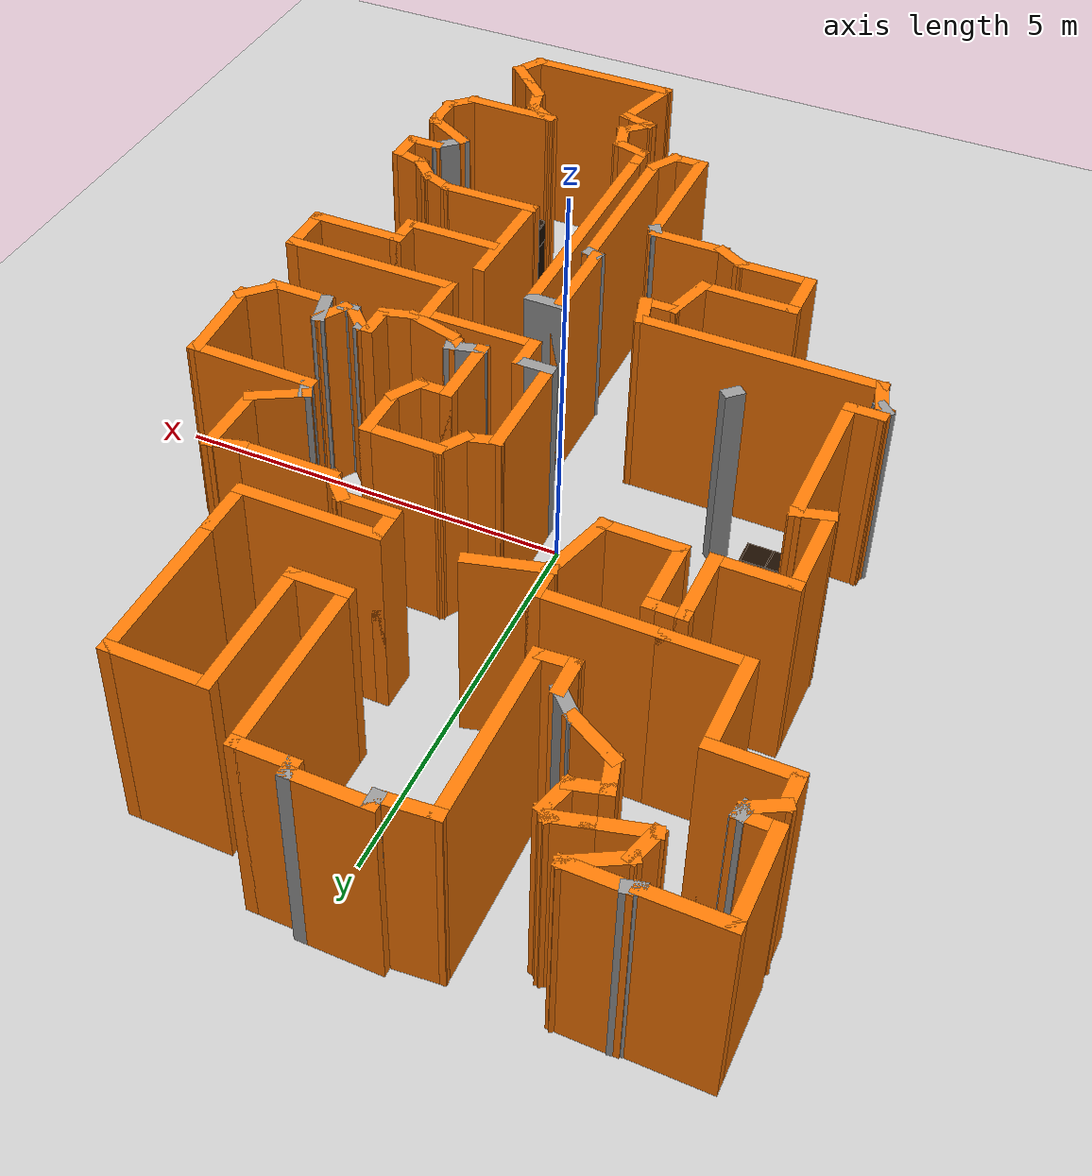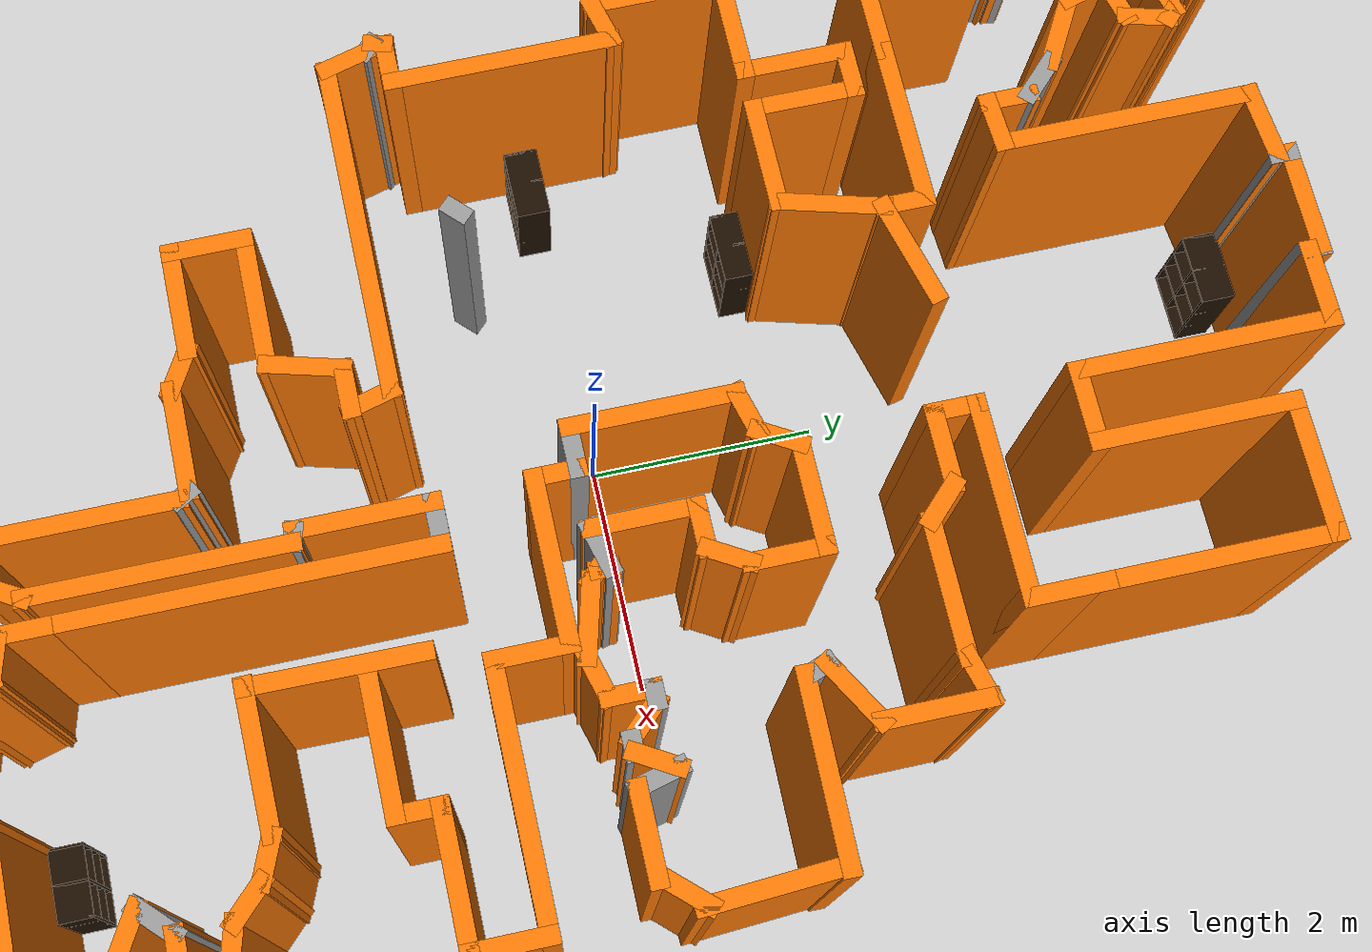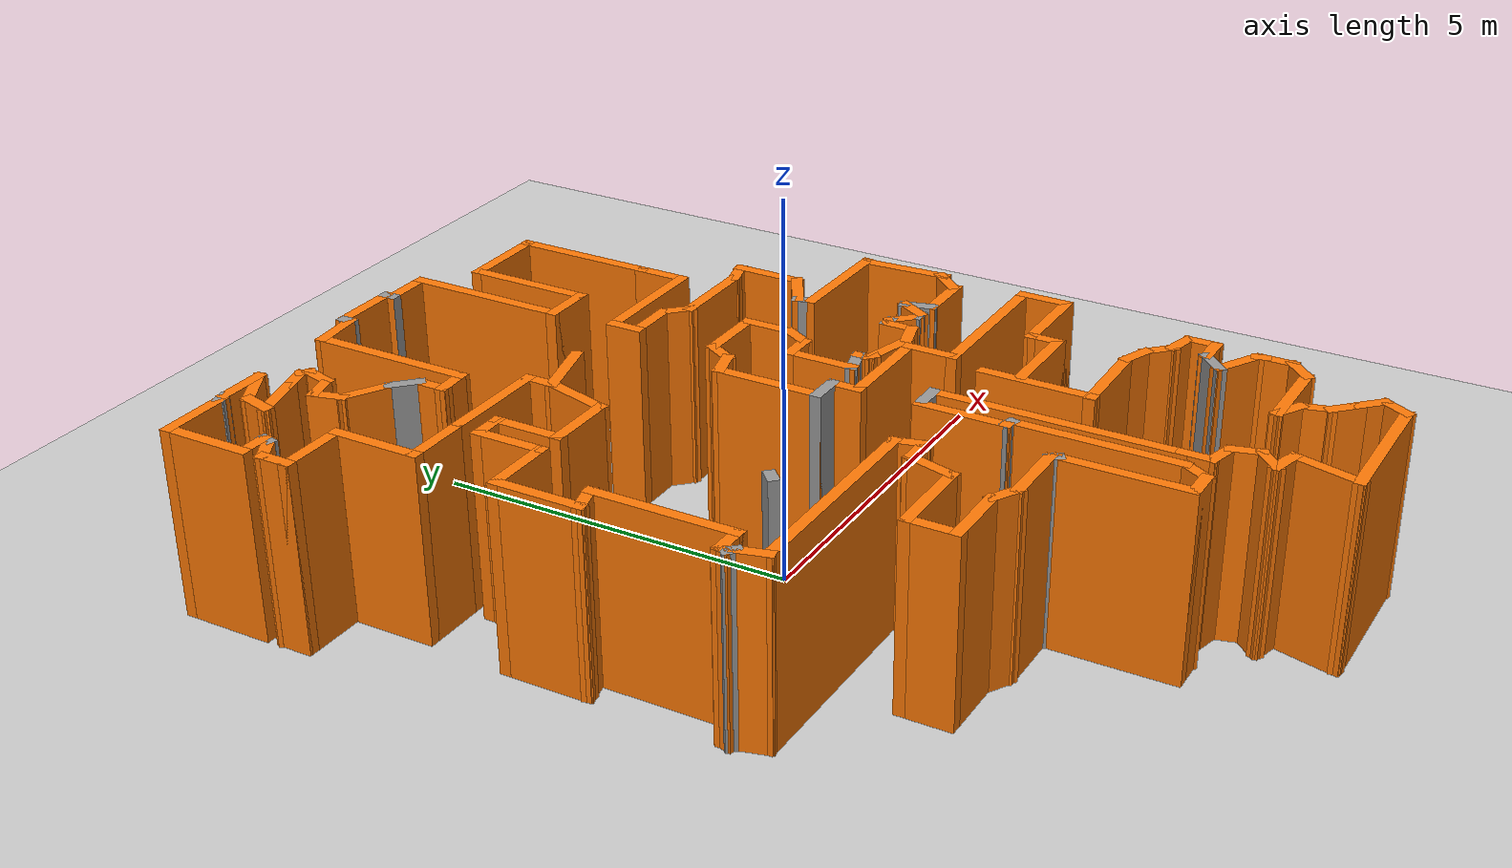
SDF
<sdf version="1.6">
 <world name="default">
  <light name="sun" type="directional">
   <pose>0 0 10 0 -0 0</pose>
   <diffuse>0.8 0.8 0.8 1</diffuse>
   <specular>0.2 0.2 0.2 1</specular>
   <attenuation>
    <range>1000</range>
    <constant>0.9</constant>
    <linear>0.01</linear>
    <quadratic>0.001</quadratic>
   </attenuation>
   <direction>-0.5 0.1 -0.9</direction>
  </light>
  <model name="ground_plane">
   <static>1</static>
   <link name="link">
    <collision name="collision">
     <geometry><plane><normal>0 0 1</normal><size>100 100</size></plane></geometry>
     <surface>
      <contact><collide_bitmask>65535</collide_bitmask></contact>
      <friction><ode><mu>100</mu><mu2>50</mu2></ode></friction>
     </surface>
    </collision>
    <visual name="visual">
     <cast_shadows>0</cast_shadows>
     <geometry><plane><normal>0 0 1</normal><size>100 100</size></plane></geometry>
     <material>
      <script><uri>file://media/materials/scripts/gazebo.material</uri><name>Gazebo/Grey</name></script>
     </material>
    </visual>
   </link>
  </model>
  <gravity>0 0 -9.8</gravity>
  <magnetic_field>6e-06 2.3e-05 -4.2e-05</magnetic_field>
  <atmosphere type="adiabatic"/>
  <physics name="default_physics" default="0" type="ode">
   <max_step_size>0.001</max_step_size>
   <real_time_factor>1</real_time_factor>
   <real_time_update_rate>1000</real_time_update_rate>
  </physics>
  <scene><ambient>0.4 0.4 0.4 1</ambient><background>0.7 0.7 0.7 1</background><shadows>1</shadows></scene>
  <audio><device>default</device></audio>
  <spherical_coordinates>
   <surface_model>EARTH_WGS84</surface_model>
   <latitude_deg>0</latitude_deg>
   <longitude_deg>0</longitude_deg>
   <elevation>0</elevation>
   <heading_deg>0</heading_deg>
  </spherical_coordinates>
  <model name="map_4">
   <pose>0.04124 -0.27835 0 0 -0 0</pose>
   <link name="Wall_0">
    <collision name="Wall_0_Collision">
     <geometry><box><size>2.25 0.15 2.5</size></box></geometry>
     <pose>0 0 1.25 0 -0 0</pose>
    </collision>
    <visual name="Wall_0_Visual">
     <pose>0 0 1.25 0 -0 0</pose>
     <geometry><box><size>2.25 0.15 2.5</size></box></geometry>
     <material>
      <script><uri>file://media/materials/scripts/gazebo.material</uri><name>Gazebo/Grey</name></script>
      <ambient>0.996078 0.47451 0.0196078 1</ambient>
     </material>
     <meta><layer>0</layer></meta>
    </visual>
    <pose>-1.38482 5.02012 0 0 -0 -1.5708</pose>
   </link>
   <link name="Wall_1">
    <collision name="Wall_1_Collision">
     <geometry><box><size>0.523847 0.15 2.5</size></box></geometry>
     <pose>0 0 1.25 0 -0 0</pose>
    </collision>
    <visual name="Wall_1_Visual">
     <pose>0 0 1.25 0 -0 0</pose>
     <geometry><box><size>0.523847 0.15 2.5</size></box></geometry>
     <material>
      <script><uri>file://media/materials/scripts/gazebo.material</uri><name>Gazebo/Grey</name></script>
      <ambient>0.996078 0.47451 0.0196078 1</ambient>
     </material>
     <meta><layer>0</layer></meta>
    </visual>
    <pose>-1.57139 3.95855 0 0 -0 -3.07968</pose>
   </link>
   <link name="Wall_100">
    <collision name="Wall_100_Collision">
     <geometry><box><size>0.5 0.15 2.5</size></box></geometry>
     <pose>0 0 1.25 0 -0 0</pose>
    </collision>
    <visual name="Wall_100_Visual">
     <pose>0 0 1.25 0 -0 0</pose>
     <geometry><box><size>0.5 0.15 2.5</size></box></geometry>
     <material>
      <script><uri>file://media/materials/scripts/gazebo.material</uri><name>Gazebo/Grey</name></script>
      <ambient>0.996078 0.47451 0.0196078 1</ambient>
     </material>
     <meta><layer>0</layer></meta>
    </visual>
    <pose>3.63966 -3.64447 0 0 -0 0</pose>
   </link>
   <link name="Wall_101">
    <collision name="Wall_101_Collision">
     <geometry><box><size>0.5 0.15 2.5</size></box></geometry>
     <pose>0 0 1.25 0 -0 0</pose>
    </collision>
    <visual name="Wall_101_Visual">
     <pose>0 0 1.25 0 -0 0</pose>
     <geometry><box><size>0.5 0.15 2.5</size></box></geometry>
     <material>
      <script><uri>file://media/materials/scripts/gazebo.material</uri><name>Gazebo/Grey</name></script>
      <ambient>0.996078 0.47451 0.0196078 1</ambient>
     </material>
     <meta><layer>0</layer></meta>
    </visual>
    <pose>3.81466 -3.46947 0 0 -0 1.5708</pose>
   </link>
   <link name="Wall_102">
    <collision name="Wall_102_Collision">
     <geometry><box><size>0.5 0.15 2.5</size></box></geometry>
     <pose>0 0 1.25 0 -0 0</pose>
    </collision>
    <visual name="Wall_102_Visual">
     <pose>0 0 1.25 0 -0 0</pose>
     <geometry><box><size>0.5 0.15 2.5</size></box></geometry>
     <material>
      <script><uri>file://media/materials/scripts/gazebo.material</uri><name>Gazebo/Grey</name></script>
      <ambient>0.996078 0.47451 0.0196078 1</ambient>
     </material>
     <meta><layer>0</layer></meta>
    </visual>
    <pose>3.64562 -3.24918 0 0 -0 2.87979</pose>
   </link>
   <link name="Wall_103">
    <collision name="Wall_103_Collision">
     <geometry><box><size>0.5 0.15 2.5</size></box></geometry>
     <pose>0 0 1.25 0 -0 0</pose>
    </collision>
    <visual name="Wall_103_Visual">
     <pose>0 0 1.25 0 -0 0</pose>
     <geometry><box><size>0.5 0.15 2.5</size></box></geometry>
     <material>
      <script><uri>file://media/materials/scripts/gazebo.material</uri><name>Gazebo/Grey</name></script>
      <ambient>0.996078 0.47451 0.0196078 1</ambient>
     </material>
     <meta><layer>0</layer></meta>
    </visual>
    <pose>3.35284 -3.08014 0 0 -0 2.35619</pose>
   </link>
   <link name="Wall_104">
    <collision name="Wall_104_Collision">
     <geometry><box><size>0.493604 0.15 2.5</size></box></geometry>
     <pose>0 0 1.25 0 -0 0</pose>
    </collision>
    <visual name="Wall_104_Visual">
     <pose>0 0 1.25 0 -0 0</pose>
     <geometry><box><size>0.493604 0.15 2.5</size></box></geometry>
     <material>
      <script><uri>file://media/materials/scripts/gazebo.material</uri><name>Gazebo/Grey</name></script>
      <ambient>0.996078 0.47451 0.0196078 1</ambient>
     </material>
     <meta><layer>0</layer></meta>
    </visual>
    <pose>3.06994 -2.89171 0 0 -0 2.75556</pose>
   </link>
   <link name="Wall_105">
    <collision name="Wall_105_Collision">
     <geometry><box><size>1.29573 0.15 2.5</size></box></geometry>
     <pose>0 0 1.25 0 -0 0</pose>
    </collision>
    <visual name="Wall_105_Visual">
     <pose>0 0 1.25 0 -0 0</pose>
     <geometry><box><size>1.29573 0.15 2.5</size></box></geometry>
     <material>
      <script><uri>file://media/materials/scripts/gazebo.material</uri><name>Gazebo/Grey</name></script>
      <ambient>0.996078 0.47451 0.0196078 1</ambient>
     </material>
     <meta><layer>0</layer></meta>
    </visual>
    <pose>2.32276 -2.83463 0 0 -0 -3.12832</pose>
   </link>
   <link name="Wall_106">
    <collision name="Wall_106_Collision">
     <geometry><box><size>1.54571 0.15 2.5</size></box></geometry>
     <pose>0 0 1.25 0 -0 0</pose>
    </collision>
    <visual name="Wall_106_Visual">
     <pose>0 0 1.25 0 -0 0</pose>
     <geometry><box><size>1.54571 0.15 2.5</size></box></geometry>
     <material>
      <script><uri>file://media/materials/scripts/gazebo.material</uri><name>Gazebo/Grey</name></script>
      <ambient>0.996078 0.47451 0.0196078 1</ambient>
     </material>
     <meta><layer>0</layer></meta>
    </visual>
    <pose>1.77276 -2.14442 0 0 -0 1.5599</pose>
   </link>
   <link name="Wall_108">
    <collision name="Wall_108_Collision">
     <geometry><box><size>1.25 0.15 2.5</size></box></geometry>
     <pose>0 0 1.25 0 -0 0</pose>
    </collision>
    <visual name="Wall_108_Visual">
     <pose>0 0 1.25 0 -0 0</pose>
     <geometry><box><size>1.25 0.15 2.5</size></box></geometry>
     <material>
      <script><uri>file://media/materials/scripts/gazebo.material</uri><name>Gazebo/Grey</name></script>
      <ambient>0.996078 0.47451 0.0196078 1</ambient>
     </material>
     <meta><layer>0</layer></meta>
    </visual>
    <pose>2.40475 -1.90642 0 0 -0 0</pose>
   </link>
   <link name="Wall_109">
    <collision name="Wall_109_Collision">
     <geometry><box><size>0.5 0.15 2.5</size></box></geometry>
     <pose>0 0 1.25 0 -0 0</pose>
    </collision>
    <visual name="Wall_109_Visual">
     <pose>0 0 1.25 0 -0 0</pose>
     <geometry><box><size>0.5 0.15 2.5</size></box></geometry>
     <material>
      <script><uri>file://media/materials/scripts/gazebo.material</uri><name>Gazebo/Grey</name></script>
      <ambient>0.996078 0.47451 0.0196078 1</ambient>
     </material>
     <meta><layer>0</layer></meta>
    </visual>
    <pose>2.95475 -1.73142 0 0 -0 1.5708</pose>
   </link>
   <link name="Wall_110">
    <collision name="Wall_110_Collision">
     <geometry><box><size>1.25 0.15 2.5</size></box></geometry>
     <pose>0 0 1.25 0 -0 0</pose>
    </collision>
    <visual name="Wall_110_Visual">
     <pose>0 0 1.25 0 -0 0</pose>
     <geometry><box><size>1.25 0.15 2.5</size></box></geometry>
     <material>
      <script><uri>file://media/materials/scripts/gazebo.material</uri><name>Gazebo/Grey</name></script>
      <ambient>0.996078 0.47451 0.0196078 1</ambient>
     </material>
     <meta><layer>0</layer></meta>
    </visual>
    <pose>3.50475 -1.55642 0 0 -0 0</pose>
   </link>
   <link name="Wall_111">
    <collision name="Wall_111_Collision">
     <geometry><box><size>0.75 0.15 2.5</size></box></geometry>
     <pose>0 0 1.25 0 -0 0</pose>
    </collision>
    <visual name="Wall_111_Visual">
     <pose>0 0 1.25 0 -0 0</pose>
     <geometry><box><size>0.75 0.15 2.5</size></box></geometry>
     <material>
      <script><uri>file://media/materials/scripts/gazebo.material</uri><name>Gazebo/Grey</name></script>
      <ambient>0.996078 0.47451 0.0196078 1</ambient>
     </material>
     <meta><layer>0</layer></meta>
    </visual>
    <pose>4.05475 -1.25642 0 0 -0 1.5708</pose>
   </link>
   <link name="Wall_112">
    <collision name="Wall_112_Collision">
     <geometry><box><size>2.25 0.15 2.5</size></box></geometry>
     <pose>0 0 1.25 0 -0 0</pose>
    </collision>
    <visual name="Wall_112_Visual">
     <pose>0 0 1.25 0 -0 0</pose>
     <geometry><box><size>2.25 0.15 2.5</size></box></geometry>
     <material>
      <script><uri>file://media/materials/scripts/gazebo.material</uri><name>Gazebo/Grey</name></script>
      <ambient>0.996078 0.47451 0.0196078 1</ambient>
     </material>
     <meta><layer>0</layer></meta>
    </visual>
    <pose>3.00475 -0.956422 0 0 -0 3.14159</pose>
   </link>
   <link name="Wall_114">
    <collision name="Wall_114_Collision">
     <geometry><box><size>0.75 0.15 2.5</size></box></geometry>
     <pose>0 0 1.25 0 -0 0</pose>
    </collision>
    <visual name="Wall_114_Visual">
     <pose>0 0 1.25 0 -0 0</pose>
     <geometry><box><size>0.75 0.15 2.5</size></box></geometry>
     <material>
      <script><uri>file://media/materials/scripts/gazebo.material</uri><name>Gazebo/Grey</name></script>
      <ambient>0.996078 0.47451 0.0196078 1</ambient>
     </material>
     <meta><layer>0</layer></meta>
    </visual>
    <pose>1.95475 -0.656423 0 0 -0 1.5708</pose>
   </link>
   <link name="Wall_115">
    <collision name="Wall_115_Collision">
     <geometry><box><size>1.5 0.15 2.5</size></box></geometry>
     <pose>0 0 1.25 0 -0 0</pose>
    </collision>
    <visual name="Wall_115_Visual">
     <pose>0 0 1.25 0 -0 0</pose>
     <geometry><box><size>1.5 0.15 2.5</size></box></geometry>
     <material>
      <script><uri>file://media/materials/scripts/gazebo.material</uri><name>Gazebo/Grey</name></script>
      <ambient>0.996078 0.47451 0.0196078 1</ambient>
     </material>
     <meta><layer>0</layer></meta>
    </visual>
    <pose>1.27975 -0.356422 0 0 -0 3.14159</pose>
   </link>
   <link name="Wall_116">
    <collision name="Wall_116_Collision">
     <geometry><box><size>0.5 0.15 2.5</size></box></geometry>
     <pose>0 0 1.25 0 -0 0</pose>
    </collision>
    <visual name="Wall_116_Visual">
     <pose>0 0 1.25 0 -0 0</pose>
     <geometry><box><size>0.5 0.15 2.5</size></box></geometry>
     <material>
      <script><uri>file://media/materials/scripts/gazebo.material</uri><name>Gazebo/Grey</name></script>
      <ambient>0.996078 0.47451 0.0196078 1</ambient>
     </material>
     <meta><layer>0</layer></meta>
    </visual>
    <pose>0.604748 -0.181422 0 0 -0 1.5708</pose>
   </link>
   <link name="Wall_117">
    <collision name="Wall_117_Collision">
     <geometry><box><size>0.5 0.15 2.5</size></box></geometry>
     <pose>0 0 1.25 0 -0 0</pose>
    </collision>
    <visual name="Wall_117_Visual">
     <pose>0 0 1.25 0 -0 0</pose>
     <geometry><box><size>0.5 0.15 2.5</size></box></geometry>
     <material>
      <script><uri>file://media/materials/scripts/gazebo.material</uri><name>Gazebo/Grey</name></script>
      <ambient>1 1 1 1</ambient>
     </material>
     <meta><layer>0</layer></meta>
    </visual>
    <pose>0.429748 -0.006423 0 0 -0 3.14159</pose>
   </link>
   <link name="Wall_118">
    <collision name="Wall_118_Collision">
     <geometry><box><size>1.5 0.15 2.5</size></box></geometry>
     <pose>0 0 1.25 0 -0 0</pose>
    </collision>
    <visual name="Wall_118_Visual">
     <pose>0 0 1.25 0 -0 0</pose>
     <geometry><box><size>1.5 0.15 2.5</size></box></geometry>
     <material>
      <script><uri>file://media/materials/scripts/gazebo.material</uri><name>Gazebo/Grey</name></script>
      <ambient>0.996078 0.47451 0.0196078 1</ambient>
     </material>
     <meta><layer>0</layer></meta>
    </visual>
    <pose>0.254748 0.668578 0 0 -0 1.5708</pose>
   </link>
   <link name="Wall_119">
    <collision name="Wall_119_Collision">
     <geometry><box><size>0.5 0.15 2.5</size></box></geometry>
     <pose>0 0 1.25 0 -0 0</pose>
    </collision>
    <visual name="Wall_119_Visual">
     <pose>0 0 1.25 0 -0 0</pose>
     <geometry><box><size>0.5 0.15 2.5</size></box></geometry>
     <material>
      <script><uri>file://media/materials/scripts/gazebo.material</uri><name>Gazebo/Grey</name></script>
      <ambient>0.996078 0.47451 0.0196078 1</ambient>
     </material>
     <meta><layer>0</layer></meta>
    </visual>
    <pose>0.423785 1.38887 0 0 -0 0.261799</pose>
   </link>
   <link name="Wall_12">
    <collision name="Wall_12_Collision">
     <geometry><box><size>0.75 0.15 2.5</size></box></geometry>
     <pose>0 0 1.25 0 -0 0</pose>
    </collision>
    <visual name="Wall_12_Visual">
     <pose>0 0 1.25 0 -0 0</pose>
     <geometry><box><size>0.75 0.15 2.5</size></box></geometry>
     <material>
      <script><uri>file://media/materials/scripts/gazebo.material</uri><name>Gazebo/Grey</name></script>
      <ambient>0.996078 0.47451 0.0196078 1</ambient>
     </material>
     <meta><layer>0</layer></meta>
    </visual>
    <pose>-2.88554 5.51369 0 0 -0 -2.87979</pose>
   </link>
   <link name="Wall_120">
    <collision name="Wall_120_Collision">
     <geometry><box><size>0.5 0.15 2.5</size></box></geometry>
     <pose>0 0 1.25 0 -0 0</pose>
    </collision>
    <visual name="Wall_120_Visual">
     <pose>0 0 1.25 0 -0 0</pose>
     <geometry><box><size>0.5 0.15 2.5</size></box></geometry>
     <material>
      <script><uri>file://media/materials/scripts/gazebo.material</uri><name>Gazebo/Grey</name></script>
      <ambient>0.996078 0.47451 0.0196078 1</ambient>
     </material>
     <meta><layer>0</layer></meta>
    </visual>
    <pose>0.680322 1.58572 0 0 -0 1.0472</pose>
   </link>
   <link name="Wall_121">
    <collision name="Wall_121_Collision">
     <geometry><box><size>1 0.15 2.5</size></box></geometry>
     <pose>0 0 1.25 0 -0 0</pose>
    </collision>
    <visual name="Wall_121_Visual">
     <pose>0 0 1.25 0 -0 0</pose>
     <geometry><box><size>1 0.15 2.5</size></box></geometry>
     <material>
      <script><uri>file://media/materials/scripts/gazebo.material</uri><name>Gazebo/Grey</name></script>
      <ambient>0.996078 0.47451 0.0196078 1</ambient>
     </material>
     <meta><layer>0</layer></meta>
    </visual>
    <pose>1.19282 1.73727 0 0 -0 0</pose>
   </link>
   <link name="Wall_122">
    <collision name="Wall_122_Collision">
     <geometry><box><size>0.75 0.15 2.5</size></box></geometry>
     <pose>0 0 1.25 0 -0 0</pose>
    </collision>
    <visual name="Wall_122_Visual">
     <pose>0 0 1.25 0 -0 0</pose>
     <geometry><box><size>0.75 0.15 2.5</size></box></geometry>
     <material>
      <script><uri>file://media/materials/scripts/gazebo.material</uri><name>Gazebo/Grey</name></script>
      <ambient>0.996078 0.47451 0.0196078 1</ambient>
     </material>
     <meta><layer>0</layer></meta>
    </visual>
    <pose>1.61782 1.43727 0 0 -0 -1.5708</pose>
   </link>
   <link name="Wall_123">
    <collision name="Wall_123_Collision">
     <geometry><box><size>0.5 0.15 2.5</size></box></geometry>
     <pose>0 0 1.25 0 -0 0</pose>
    </collision>
    <visual name="Wall_123_Visual">
     <pose>0 0 1.25 0 -0 0</pose>
     <geometry><box><size>0.5 0.15 2.5</size></box></geometry>
     <material>
      <script><uri>file://media/materials/scripts/gazebo.material</uri><name>Gazebo/Grey</name></script>
      <ambient>0.996078 0.47451 0.0196078 1</ambient>
     </material>
     <meta><layer>0</layer></meta>
    </visual>
    <pose>1.53032 0.985719 0 0 -0 -2.0944</pose>
   </link>
   <link name="Wall_124">
    <collision name="Wall_124_Collision">
     <geometry><box><size>0.5 0.15 2.5</size></box></geometry>
     <pose>0 0 1.25 0 -0 0</pose>
    </collision>
    <visual name="Wall_124_Visual">
     <pose>0 0 1.25 0 -0 0</pose>
     <geometry><box><size>0.5 0.15 2.5</size></box></geometry>
     <material>
      <script><uri>file://media/materials/scripts/gazebo.material</uri><name>Gazebo/Grey</name></script>
      <ambient>0.996078 0.47451 0.0196078 1</ambient>
     </material>
     <meta><layer>0</layer></meta>
    </visual>
    <pose>1.26782 0.834164 0 0 -0 3.14159</pose>
   </link>
   <link name="Wall_125">
    <collision name="Wall_125_Collision">
     <geometry><box><size>1 0.15 2.5</size></box></geometry>
     <pose>0 0 1.25 0 -0 0</pose>
    </collision>
    <visual name="Wall_125_Visual">
     <pose>0 0 1.25 0 -0 0</pose>
     <geometry><box><size>1 0.15 2.5</size></box></geometry>
     <material>
      <script><uri>file://media/materials/scripts/gazebo.material</uri><name>Gazebo/Grey</name></script>
      <ambient>0.996078 0.47451 0.0196078 1</ambient>
     </material>
     <meta><layer>0</layer></meta>
    </visual>
    <pose>1.09282 0.409164 0 0 -0 -1.5708</pose>
   </link>
   <link name="Wall_126">
    <collision name="Wall_126_Collision">
     <geometry><box><size>0.5 0.15 2.5</size></box></geometry>
     <pose>0 0 1.25 0 -0 0</pose>
    </collision>
    <visual name="Wall_126_Visual">
     <pose>0 0 1.25 0 -0 0</pose>
     <geometry><box><size>0.5 0.15 2.5</size></box></geometry>
     <material>
      <script><uri>file://media/materials/scripts/gazebo.material</uri><name>Gazebo/Grey</name></script>
      <ambient>1 1 1 1</ambient>
     </material>
     <meta><layer>0</layer></meta>
    </visual>
    <pose>1.26186 0.029458 0 0 -0 0.261799</pose>
   </link>
   <link name="Wall_129">
    <collision name="Wall_129_Collision">
     <geometry><box><size>0.25 0.15 2.5</size></box></geometry>
     <pose>0 0 1.25 0 -0 0</pose>
    </collision>
    <visual name="Wall_129_Visual">
     <pose>0 0 1.25 0 -0 0</pose>
     <geometry><box><size>0.25 0.15 2.5</size></box></geometry>
     <material>
      <script><uri>file://media/materials/scripts/gazebo.material</uri><name>Gazebo/Grey</name></script>
      <ambient>0.996078 0.47451 0.0196078 1</ambient>
     </material>
     <meta><layer>0</layer></meta>
    </visual>
    <pose>1.4309 0.024751 0 0 -0 -1.5708</pose>
   </link>
   <link name="Wall_13">
    <collision name="Wall_13_Collision">
     <geometry><box><size>0.5 0.15 2.5</size></box></geometry>
     <pose>0 0 1.25 0 -0 0</pose>
    </collision>
    <visual name="Wall_13_Visual">
     <pose>0 0 1.25 0 -0 0</pose>
     <geometry><box><size>0.5 0.15 2.5</size></box></geometry>
     <material>
      <script><uri>file://media/materials/scripts/gazebo.material</uri><name>Gazebo/Grey</name></script>
      <ambient>0.996078 0.47451 0.0196078 1</ambient>
     </material>
     <meta><layer>0</layer></meta>
    </visual>
    <pose>-3.13003 5.60508 0 0 -0 1.309</pose>
   </link>
   <link name="Wall_130">
    <collision name="Wall_130_Collision">
     <geometry><box><size>0.25 0.15 2.5</size></box></geometry>
     <pose>0 0 1.25 0 -0 0</pose>
    </collision>
    <visual name="Wall_130_Visual">
     <pose>0 0 1.25 0 -0 0</pose>
     <geometry><box><size>0.25 0.15 2.5</size></box></geometry>
     <material>
      <script><uri>file://media/materials/scripts/gazebo.material</uri><name>Gazebo/Grey</name></script>
      <ambient>0.996078 0.47451 0.0196078 1</ambient>
     </material>
     <meta><layer>0</layer></meta>
    </visual>
    <pose>1.46625 -0.060605 0 0 -0 -0.785398</pose>
   </link>
   <link name="Wall_131">
    <collision name="Wall_131_Collision">
     <geometry><box><size>0.75 0.15 2.5</size></box></geometry>
     <pose>0 0 1.25 0 -0 0</pose>
    </collision>
    <visual name="Wall_131_Visual">
     <pose>0 0 1.25 0 -0 0</pose>
     <geometry><box><size>0.75 0.15 2.5</size></box></geometry>
     <material>
      <script><uri>file://media/materials/scripts/gazebo.material</uri><name>Gazebo/Grey</name></script>
      <ambient>0.996078 0.47451 0.0196078 1</ambient>
     </material>
     <meta><layer>0</layer></meta>
    </visual>
    <pose>1.79138 -0.173606 0 0 -0 -0.261799</pose>
   </link>
   <link name="Wall_132">
    <collision name="Wall_132_Collision">
     <geometry><box><size>0.5 0.15 2.5</size></box></geometry>
     <pose>0 0 1.25 0 -0 0</pose>
    </collision>
    <visual name="Wall_132_Visual">
     <pose>0 0 1.25 0 -0 0</pose>
     <geometry><box><size>0.5 0.15 2.5</size></box></geometry>
     <material>
      <script><uri>file://media/materials/scripts/gazebo.material</uri><name>Gazebo/Grey</name></script>
      <ambient>0.996078 0.47451 0.0196078 1</ambient>
     </material>
     <meta><layer>0</layer></meta>
    </visual>
    <pose>2.2502 -0.205958 0 0 -0 0.261799</pose>
   </link>
   <link name="Wall_133">
    <collision name="Wall_133_Collision">
     <geometry><box><size>0.5 0.15 2.5</size></box></geometry>
     <pose>0 0 1.25 0 -0 0</pose>
    </collision>
    <visual name="Wall_133_Visual">
     <pose>0 0 1.25 0 -0 0</pose>
     <geometry><box><size>0.5 0.15 2.5</size></box></geometry>
     <material>
      <script><uri>file://media/materials/scripts/gazebo.material</uri><name>Gazebo/Grey</name></script>
      <ambient>0.996078 0.47451 0.0196078 1</ambient>
     </material>
     <meta><layer>0</layer></meta>
    </visual>
    <pose>2.41924 0.014336 0 0 -0 1.5708</pose>
   </link>
   <link name="Wall_134">
    <collision name="Wall_134_Collision">
     <geometry><box><size>0.25 0.15 2.5</size></box></geometry>
     <pose>0 0 1.25 0 -0 0</pose>
    </collision>
    <visual name="Wall_134_Visual">
     <pose>0 0 1.25 0 -0 0</pose>
     <geometry><box><size>0.25 0.15 2.5</size></box></geometry>
     <material>
      <script><uri>file://media/materials/scripts/gazebo.material</uri><name>Gazebo/Grey</name></script>
      <ambient>1 1 1 1</ambient>
     </material>
     <meta><layer>0</layer></meta>
    </visual>
    <pose>2.46924 0.189335 0 0 -0 0</pose>
   </link>
   <link name="Wall_135">
    <collision name="Wall_135_Collision">
     <geometry><box><size>0.5 0.15 2.5</size></box></geometry>
     <pose>0 0 1.25 0 -0 0</pose>
    </collision>
    <visual name="Wall_135_Visual">
     <pose>0 0 1.25 0 -0 0</pose>
     <geometry><box><size>0.5 0.15 2.5</size></box></geometry>
     <material>
      <script><uri>file://media/materials/scripts/gazebo.material</uri><name>Gazebo/Grey</name></script>
      <ambient>0.996078 0.47451 0.0196078 1</ambient>
     </material>
     <meta><layer>0</layer></meta>
    </visual>
    <pose>2.64298 0.065592 0 0 -0 -0.785398</pose>
   </link>
   <link name="Wall_136">
    <collision name="Wall_136_Collision">
     <geometry><box><size>0.25 0.15 2.5</size></box></geometry>
     <pose>0 0 1.25 0 -0 0</pose>
    </collision>
    <visual name="Wall_136_Visual">
     <pose>0 0 1.25 0 -0 0</pose>
     <geometry><box><size>0.25 0.15 2.5</size></box></geometry>
     <material>
      <script><uri>file://media/materials/scripts/gazebo.material</uri><name>Gazebo/Grey</name></script>
      <ambient>1 1 1 1</ambient>
     </material>
     <meta><layer>0</layer></meta>
    </visual>
    <pose>2.81672 -0.058152 0 0 -0 0</pose>
   </link>
   <link name="Wall_137">
    <collision name="Wall_137_Collision">
     <geometry><box><size>0.5 0.15 2.5</size></box></geometry>
     <pose>0 0 1.25 0 -0 0</pose>
    </collision>
    <visual name="Wall_137_Visual">
     <pose>0 0 1.25 0 -0 0</pose>
     <geometry><box><size>0.5 0.15 2.5</size></box></geometry>
     <material>
      <script><uri>file://media/materials/scripts/gazebo.material</uri><name>Gazebo/Grey</name></script>
      <ambient>0.996078 0.47451 0.0196078 1</ambient>
     </material>
     <meta><layer>0</layer></meta>
    </visual>
    <pose>2.95422 0.093402 0 0 -0 1.0472</pose>
   </link>
   <link name="Wall_138">
    <collision name="Wall_138_Collision">
     <geometry><box><size>0.5 0.15 2.5</size></box></geometry>
     <pose>0 0 1.25 0 -0 0</pose>
    </collision>
    <visual name="Wall_138_Visual">
     <pose>0 0 1.25 0 -0 0</pose>
     <geometry><box><size>0.5 0.15 2.5</size></box></geometry>
     <material>
      <script><uri>file://media/materials/scripts/gazebo.material</uri><name>Gazebo/Grey</name></script>
      <ambient>1 1 1 1</ambient>
     </material>
     <meta><layer>0</layer></meta>
    </visual>
    <pose>3.08702 0.07592 0 0 -0 -1.309</pose>
   </link>
   <link name="Wall_139">
    <collision name="Wall_139_Collision">
     <geometry><box><size>0.842522 0.15 2.5</size></box></geometry>
     <pose>0 0 1.25 0 -0 0</pose>
    </collision>
    <visual name="Wall_139_Visual">
     <pose>0 0 1.25 0 -0 0</pose>
     <geometry><box><size>0.842522 0.15 2.5</size></box></geometry>
     <material>
      <script><uri>file://media/materials/scripts/gazebo.material</uri><name>Gazebo/Grey</name></script>
      <ambient>0.996078 0.47451 0.0196078 1</ambient>
     </material>
     <meta><layer>0</layer></meta>
    </visual>
    <pose>3.47857 -0.093117 0 0 -0 0</pose>
   </link>
   <link name="Wall_14">
    <collision name="Wall_14_Collision">
     <geometry><box><size>0.75 0.15 2.5</size></box></geometry>
     <pose>0 0 1.25 0 -0 0</pose>
    </collision>
    <visual name="Wall_14_Visual">
     <pose>0 0 1.25 0 -0 0</pose>
     <geometry><box><size>0.75 0.15 2.5</size></box></geometry>
     <material>
      <script><uri>file://media/materials/scripts/gazebo.material</uri><name>Gazebo/Grey</name></script>
      <ambient>0.996078 0.47451 0.0196078 1</ambient>
     </material>
     <meta><layer>0</layer></meta>
    </visual>
    <pose>-2.82493 5.92412 0 0 -0 0.523599</pose>
   </link>
   <link name="Wall_140">
    <collision name="Wall_140_Collision">
     <geometry><box><size>0.53772 0.15 2.5</size></box></geometry>
     <pose>0 0 1.25 0 -0 0</pose>
    </collision>
    <visual name="Wall_140_Visual">
     <pose>0 0 1.25 0 -0 0</pose>
     <geometry><box><size>0.53772 0.15 2.5</size></box></geometry>
     <material>
      <script><uri>file://media/materials/scripts/gazebo.material</uri><name>Gazebo/Grey</name></script>
      <ambient>0.996078 0.47451 0.0196078 1</ambient>
     </material>
     <meta><layer>0</layer></meta>
    </visual>
    <pose>3.95601 0.095884 0 0 -0 0.827595</pose>
   </link>
   <link name="Wall_141">
    <collision name="Wall_141_Collision">
     <geometry><box><size>1.27527 0.15 2.5</size></box></geometry>
     <pose>0 0 1.25 0 -0 0</pose>
    </collision>
    <visual name="Wall_141_Visual">
     <pose>0 0 1.25 0 -0 0</pose>
     <geometry><box><size>1.27527 0.15 2.5</size></box></geometry>
     <material>
      <script><uri>file://media/materials/scripts/gazebo.material</uri><name>Gazebo/Grey</name></script>
      <ambient>0.996078 0.47451 0.0196078 1</ambient>
     </material>
     <meta><layer>0</layer></meta>
    </visual>
    <pose>4.05249 0.753929 0 0 -0 1.6325</pose>
   </link>
   <link name="Wall_142">
    <collision name="Wall_142_Collision">
     <geometry><box><size>1.63453 0.15 2.5</size></box></geometry>
     <pose>0 0 1.25 0 -0 0</pose>
    </collision>
    <visual name="Wall_142_Visual">
     <pose>0 0 1.25 0 -0 0</pose>
     <geometry><box><size>1.63453 0.15 2.5</size></box></geometry>
     <material>
      <script><uri>file://media/materials/scripts/gazebo.material</uri><name>Gazebo/Grey</name></script>
      <ambient>0.996078 0.47451 0.0196078 1</ambient>
     </material>
     <meta><layer>0</layer></meta>
    </visual>
    <pose>3.29875 1.32706 0 0 -0 3.12601</pose>
   </link>
   <link name="Wall_143">
    <collision name="Wall_143_Collision">
     <geometry><box><size>0.29196 0.15 2.5</size></box></geometry>
     <pose>0 0 1.25 0 -0 0</pose>
    </collision>
    <visual name="Wall_143_Visual">
     <pose>0 0 1.25 0 -0 0</pose>
     <geometry><box><size>0.29196 0.15 2.5</size></box></geometry>
     <material>
      <script><uri>file://media/materials/scripts/gazebo.material</uri><name>Gazebo/Grey</name></script>
      <ambient>1 1 1 1</ambient>
     </material>
     <meta><layer>0</layer></meta>
    </visual>
    <pose>2.53157 1.45132 0 0 -0 1.93073</pose>
   </link>
   <link name="Wall_144">
    <collision name="Wall_144_Collision">
     <geometry><box><size>0.75 0.15 2.5</size></box></geometry>
     <pose>0 0 1.25 0 -0 0</pose>
    </collision>
    <visual name="Wall_144_Visual">
     <pose>0 0 1.25 0 -0 0</pose>
     <geometry><box><size>0.75 0.15 2.5</size></box></geometry>
     <material>
      <script><uri>file://media/materials/scripts/gazebo.material</uri><name>Gazebo/Grey</name></script>
      <ambient>0.996078 0.47451 0.0196078 1</ambient>
     </material>
     <meta><layer>0</layer></meta>
    </visual>
    <pose>2.76638 1.66775 0 0 -0 0.523599</pose>
   </link>
   <link name="Wall_146">
    <collision name="Wall_146_Collision">
     <geometry><box><size>1 0.15 2.5</size></box></geometry>
     <pose>0 0 1.25 0 -0 0</pose>
    </collision>
    <visual name="Wall_146_Visual">
     <pose>0 0 1.25 0 -0 0</pose>
     <geometry><box><size>1 0.15 2.5</size></box></geometry>
     <material>
      <script><uri>file://media/materials/scripts/gazebo.material</uri><name>Gazebo/Grey</name></script>
      <ambient>0.996078 0.47451 0.0196078 1</ambient>
     </material>
     <meta><layer>0</layer></meta>
    </visual>
    <pose>3.02619 2.24275 0 0 -0 1.5708</pose>
   </link>
   <link name="Wall_147">
    <collision name="Wall_147_Collision">
     <geometry><box><size>0.5 0.15 2.5</size></box></geometry>
     <pose>0 0 1.25 0 -0 0</pose>
    </collision>
    <visual name="Wall_147_Visual">
     <pose>0 0 1.25 0 -0 0</pose>
     <geometry><box><size>0.5 0.15 2.5</size></box></geometry>
     <material>
      <script><uri>file://media/materials/scripts/gazebo.material</uri><name>Gazebo/Grey</name></script>
      <ambient>0.996078 0.47451 0.0196078 1</ambient>
     </material>
     <meta><layer>0</layer></meta>
    </visual>
    <pose>2.85715 2.62246 0 0 -0 -2.87979</pose>
   </link>
   <link name="Wall_148">
    <collision name="Wall_148_Collision">
     <geometry><box><size>1.25 0.15 2.5</size></box></geometry>
     <pose>0 0 1.25 0 -0 0</pose>
    </collision>
    <visual name="Wall_148_Visual">
     <pose>0 0 1.25 0 -0 0</pose>
     <geometry><box><size>1.25 0.15 2.5</size></box></geometry>
     <material>
      <script><uri>file://media/materials/scripts/gazebo.material</uri><name>Gazebo/Grey</name></script>
      <ambient>0.996078 0.47451 0.0196078 1</ambient>
     </material>
     <meta><layer>0</layer></meta>
    </visual>
    <pose>2.13811 2.57716 0 0 -0 3.14159</pose>
   </link>
   <link name="Wall_149">
    <collision name="Wall_149_Collision">
     <geometry><box><size>0.5 0.15 2.5</size></box></geometry>
     <pose>0 0 1.25 0 -0 0</pose>
    </collision>
    <visual name="Wall_149_Visual">
     <pose>0 0 1.25 0 -0 0</pose>
     <geometry><box><size>0.5 0.15 2.5</size></box></geometry>
     <material>
      <script><uri>file://media/materials/scripts/gazebo.material</uri><name>Gazebo/Grey</name></script>
      <ambient>0.996078 0.47451 0.0196078 1</ambient>
     </material>
     <meta><layer>0</layer></meta>
    </visual>
    <pose>1.46437 2.70091 0 0 -0 2.35619</pose>
   </link>
   <link name="Wall_15">
    <collision name="Wall_15_Collision">
     <geometry><box><size>0.75 0.15 2.5</size></box></geometry>
     <pose>0 0 1.25 0 -0 0</pose>
    </collision>
    <visual name="Wall_15_Visual">
     <pose>0 0 1.25 0 -0 0</pose>
     <geometry><box><size>0.75 0.15 2.5</size></box></geometry>
     <material>
      <script><uri>file://media/materials/scripts/gazebo.material</uri><name>Gazebo/Grey</name></script>
      <ambient>0.996078 0.47451 0.0196078 1</ambient>
     </material>
     <meta><layer>0</layer></meta>
    </visual>
    <pose>-2.86512 6.07412 0 0 -0 3.14159</pose>
   </link>
   <link name="Wall_150">
    <collision name="Wall_150_Collision">
     <geometry><box><size>0.75 0.15 2.5</size></box></geometry>
     <pose>0 0 1.25 0 -0 0</pose>
    </collision>
    <visual name="Wall_150_Visual">
     <pose>0 0 1.25 0 -0 0</pose>
     <geometry><box><size>0.75 0.15 2.5</size></box></geometry>
     <material>
      <script><uri>file://media/materials/scripts/gazebo.material</uri><name>Gazebo/Grey</name></script>
      <ambient>0.996078 0.47451 0.0196078 1</ambient>
     </material>
     <meta><layer>0</layer></meta>
    </visual>
    <pose>1.04063 2.82465 0 0 -0 3.14159</pose>
   </link>
   <link name="Wall_151">
    <collision name="Wall_151_Collision">
     <geometry><box><size>0.5 0.15 2.5</size></box></geometry>
     <pose>0 0 1.25 0 -0 0</pose>
    </collision>
    <visual name="Wall_151_Visual">
     <pose>0 0 1.25 0 -0 0</pose>
     <geometry><box><size>0.5 0.15 2.5</size></box></geometry>
     <material>
      <script><uri>file://media/materials/scripts/gazebo.material</uri><name>Gazebo/Grey</name></script>
      <ambient>0.996078 0.47451 0.0196078 1</ambient>
     </material>
     <meta><layer>0</layer></meta>
    </visual>
    <pose>0.740628 2.99965 0 0 -0 1.5708</pose>
   </link>
   <link name="Wall_152">
    <collision name="Wall_152_Collision">
     <geometry><box><size>1.75 0.15 2.5</size></box></geometry>
     <pose>0 0 1.25 0 -0 0</pose>
    </collision>
    <visual name="Wall_152_Visual">
     <pose>0 0 1.25 0 -0 0</pose>
     <geometry><box><size>1.75 0.15 2.5</size></box></geometry>
     <material>
      <script><uri>file://media/materials/scripts/gazebo.material</uri><name>Gazebo/Grey</name></script>
      <ambient>0.996078 0.47451 0.0196078 1</ambient>
     </material>
     <meta><layer>0</layer></meta>
    </visual>
    <pose>1.54063 3.17465 0 0 -0 0</pose>
   </link>
   <link name="Wall_153">
    <collision name="Wall_153_Collision">
     <geometry><box><size>0.75 0.15 2.5</size></box></geometry>
     <pose>0 0 1.25 0 -0 0</pose>
    </collision>
    <visual name="Wall_153_Visual">
     <pose>0 0 1.25 0 -0 0</pose>
     <geometry><box><size>0.75 0.15 2.5</size></box></geometry>
     <material>
      <script><uri>file://media/materials/scripts/gazebo.material</uri><name>Gazebo/Grey</name></script>
      <ambient>0.996078 0.47451 0.0196078 1</ambient>
     </material>
     <meta><layer>0</layer></meta>
    </visual>
    <pose>2.34063 3.47465 0 0 -0 1.5708</pose>
   </link>
   <link name="Wall_154">
    <collision name="Wall_154_Collision">
     <geometry><box><size>2 0.15 2.5</size></box></geometry>
     <pose>0 0 1.25 0 -0 0</pose>
    </collision>
    <visual name="Wall_154_Visual">
     <pose>0 0 1.25 0 -0 0</pose>
     <geometry><box><size>2 0.15 2.5</size></box></geometry>
     <material>
      <script><uri>file://media/materials/scripts/gazebo.material</uri><name>Gazebo/Grey</name></script>
      <ambient>0.996078 0.47451 0.0196078 1</ambient>
     </material>
     <meta><layer>0</layer></meta>
    </visual>
    <pose>2.34063 4.69965 0 0 -0 1.5708</pose>
   </link>
   <link name="Wall_159">
    <collision name="Wall_159_Collision">
     <geometry><box><size>1.25 0.15 2.5</size></box></geometry>
     <pose>0 0 1.25 0 -0 0</pose>
    </collision>
    <visual name="Wall_159_Visual">
     <pose>0 0 1.25 0 -0 0</pose>
     <geometry><box><size>1.25 0.15 2.5</size></box></geometry>
     <material>
      <script><uri>file://media/materials/scripts/gazebo.material</uri><name>Gazebo/Grey</name></script>
      <ambient>0.996078 0.47451 0.0196078 1</ambient>
     </material>
     <meta><layer>0</layer></meta>
    </visual>
    <pose>1.79063 5.62465 0 0 -0 3.14159</pose>
   </link>
   <link name="Wall_16">
    <collision name="Wall_16_Collision">
     <geometry><box><size>0.25 0.15 2.5</size></box></geometry>
     <pose>0 0 1.25 0 -0 0</pose>
    </collision>
    <visual name="Wall_16_Visual">
     <pose>0 0 1.25 0 -0 0</pose>
     <geometry><box><size>0.25 0.15 2.5</size></box></geometry>
     <material>
      <script><uri>file://media/materials/scripts/gazebo.material</uri><name>Gazebo/Grey</name></script>
      <ambient>1 1 1 1</ambient>
     </material>
     <meta><layer>0</layer></meta>
    </visual>
    <pose>-3.21341 6.06118 0 0 -0 -2.87979</pose>
   </link>
   <link name="Wall_160">
    <collision name="Wall_160_Collision">
     <geometry><box><size>1.75 0.15 2.5</size></box></geometry>
     <pose>0 0 1.25 0 -0 0</pose>
    </collision>
    <visual name="Wall_160_Visual">
     <pose>0 0 1.25 0 -0 0</pose>
     <geometry><box><size>1.75 0.15 2.5</size></box></geometry>
     <material>
      <script><uri>file://media/materials/scripts/gazebo.material</uri><name>Gazebo/Grey</name></script>
      <ambient>0.996078 0.47451 0.0196078 1</ambient>
     </material>
     <meta><layer>0</layer></meta>
    </visual>
    <pose>1.24063 4.82465 0 0 -0 -1.5708</pose>
   </link>
   <link name="Wall_161">
    <collision name="Wall_161_Collision">
     <geometry><box><size>0.75 0.15 2.5</size></box></geometry>
     <pose>0 0 1.25 0 -0 0</pose>
    </collision>
    <visual name="Wall_161_Visual">
     <pose>0 0 1.25 0 -0 0</pose>
     <geometry><box><size>0.75 0.15 2.5</size></box></geometry>
     <material>
      <script><uri>file://media/materials/scripts/gazebo.material</uri><name>Gazebo/Grey</name></script>
      <ambient>0.996078 0.47451 0.0196078 1</ambient>
     </material>
     <meta><layer>0</layer></meta>
    </visual>
    <pose>0.940628 4.02465 0 0 -0 3.14159</pose>
   </link>
   <link name="Wall_162">
    <collision name="Wall_162_Collision">
     <geometry><box><size>2.25 0.15 2.5</size></box></geometry>
     <pose>0 0 1.25 0 -0 0</pose>
    </collision>
    <visual name="Wall_162_Visual">
     <pose>0 0 1.25 0 -0 0</pose>
     <geometry><box><size>2.25 0.15 2.5</size></box></geometry>
     <material>
      <script><uri>file://media/materials/scripts/gazebo.material</uri><name>Gazebo/Grey</name></script>
      <ambient>0.996078 0.47451 0.0196078 1</ambient>
     </material>
     <meta><layer>0</layer></meta>
    </visual>
    <pose>0.640628 5.07465 0 0 -0 1.5708</pose>
   </link>
   <link name="Wall_163">
    <collision name="Wall_163_Collision">
     <geometry><box><size>0.75 0.15 2.5</size></box></geometry>
     <pose>0 0 1.25 0 -0 0</pose>
    </collision>
    <visual name="Wall_163_Visual">
     <pose>0 0 1.25 0 -0 0</pose>
     <geometry><box><size>0.75 0.15 2.5</size></box></geometry>
     <material>
      <script><uri>file://media/materials/scripts/gazebo.material</uri><name>Gazebo/Grey</name></script>
      <ambient>0.996078 0.47451 0.0196078 1</ambient>
     </material>
     <meta><layer>0</layer></meta>
    </visual>
    <pose>0.340628 6.12465 0 0 -0 3.14159</pose>
   </link>
   <link name="Wall_164">
    <collision name="Wall_164_Collision">
     <geometry><box><size>0.25 0.15 2.5</size></box></geometry>
     <pose>0 0 1.25 0 -0 0</pose>
    </collision>
    <visual name="Wall_164_Visual">
     <pose>0 0 1.25 0 -0 0</pose>
     <geometry><box><size>0.25 0.15 2.5</size></box></geometry>
     <material>
      <script><uri>file://media/materials/scripts/gazebo.material</uri><name>Gazebo/Grey</name></script>
      <ambient>1 1 1 1</ambient>
     </material>
     <meta><layer>0</layer></meta>
    </visual>
    <pose>0.040628 6.17465 0 0 -0 1.5708</pose>
   </link>
   <link name="Wall_165">
    <collision name="Wall_165_Collision">
     <geometry><box><size>1 0.15 2.5</size></box></geometry>
     <pose>0 0 1.25 0 -0 0</pose>
    </collision>
    <visual name="Wall_165_Visual">
     <pose>0 0 1.25 0 -0 0</pose>
     <geometry><box><size>1 0.15 2.5</size></box></geometry>
     <material>
      <script><uri>file://media/materials/scripts/gazebo.material</uri><name>Gazebo/Grey</name></script>
      <ambient>0.996078 0.47451 0.0196078 1</ambient>
     </material>
     <meta><layer>0</layer></meta>
    </visual>
    <pose>-0.384372 6.22465 0 0 -0 3.14159</pose>
   </link>
   <link name="Wall_166">
    <collision name="Wall_166_Collision">
     <geometry><box><size>0.25 0.15 2.5</size></box></geometry>
     <pose>0 0 1.25 0 -0 0</pose>
    </collision>
    <visual name="Wall_166_Visual">
     <pose>0 0 1.25 0 -0 0</pose>
     <geometry><box><size>0.25 0.15 2.5</size></box></geometry>
     <material>
      <script><uri>file://media/materials/scripts/gazebo.material</uri><name>Gazebo/Grey</name></script>
      <ambient>1 1 1 1</ambient>
     </material>
     <meta><layer>0</layer></meta>
    </visual>
    <pose>-0.809372 6.17465 0 0 -0 -1.5708</pose>
   </link>
   <link name="Wall_167">
    <collision name="Wall_167_Collision">
     <geometry><box><size>0.728027 0.15 2.5</size></box></geometry>
     <pose>0 0 1.25 0 -0 0</pose>
    </collision>
    <visual name="Wall_167_Visual">
     <pose>0 0 1.25 0 -0 0</pose>
     <geometry><box><size>0.728027 0.15 2.5</size></box></geometry>
     <material>
      <script><uri>file://media/materials/scripts/gazebo.material</uri><name>Gazebo/Grey</name></script>
      <ambient>0.996078 0.47451 0.0196078 1</ambient>
     </material>
     <meta><layer>0</layer></meta>
    </visual>
    <pose>-1.0971 6.09739 0 0 -0 -3.04711</pose>
   </link>
   <link name="Wall_17">
    <collision name="Wall_17_Collision">
     <geometry><box><size>1 0.15 2.5</size></box></geometry>
     <pose>0 0 1.25 0 -0 0</pose>
    </collision>
    <visual name="Wall_17_Visual">
     <pose>0 0 1.25 0 -0 0</pose>
     <geometry><box><size>1 0.15 2.5</size></box></geometry>
     <material>
      <script><uri>file://media/materials/scripts/gazebo.material</uri><name>Gazebo/Grey</name></script>
      <ambient>0.996078 0.47451 0.0196078 1</ambient>
     </material>
     <meta><layer>0</layer></meta>
    </visual>
    <pose>-3.68671 6.04824 0 0 -0 3.14159</pose>
   </link>
   <link name="Wall_176">
    <collision name="Wall_176_Collision">
     <geometry><box><size>1 0.15 2.5</size></box></geometry>
     <pose>0 0 1.25 0 -0 0</pose>
    </collision>
    <visual name="Wall_176_Visual">
     <pose>0 0 1.25 0 -0 0</pose>
     <geometry><box><size>1 0.15 2.5</size></box></geometry>
     <material>
      <script><uri>file://media/materials/scripts/gazebo.material</uri><name>Gazebo/Grey</name></script>
      <ambient>0.996078 0.47451 0.0196078 1</ambient>
     </material>
     <meta><layer>0</layer></meta>
    </visual>
    <pose>-0.630183 2.98664 0 0 -0 0.261799</pose>
   </link>
   <link name="Wall_18">
    <collision name="Wall_18_Collision">
     <geometry><box><size>1.25 0.15 2.5</size></box></geometry>
     <pose>0 0 1.25 0 -0 0</pose>
    </collision>
    <visual name="Wall_18_Visual">
     <pose>0 0 1.25 0 -0 0</pose>
     <geometry><box><size>1.25 0.15 2.5</size></box></geometry>
     <material>
      <script><uri>file://media/materials/scripts/gazebo.material</uri><name>Gazebo/Grey</name></script>
      <ambient>0.996078 0.47451 0.0196078 1</ambient>
     </material>
     <meta><layer>0</layer></meta>
    </visual>
    <pose>-4.11171 5.49824 0 0 -0 -1.5708</pose>
   </link>
   <link name="Wall_182">
    <collision name="Wall_182_Collision">
     <geometry><box><size>0.25 0.15 2.5</size></box></geometry>
     <pose>0 0 1.25 0 -0 0</pose>
    </collision>
    <visual name="Wall_182_Visual">
     <pose>0 0 1.25 0 -0 0</pose>
     <geometry><box><size>0.25 0.15 2.5</size></box></geometry>
     <material>
      <script><uri>file://media/materials/scripts/gazebo.material</uri><name>Gazebo/Grey</name></script>
      <ambient>1 1 1 1</ambient>
     </material>
     <meta><layer>0</layer></meta>
    </visual>
    <pose>-1.73175 -0.506693 0 0 -0 -2.35619</pose>
   </link>
   <link name="Wall_19">
    <collision name="Wall_19_Collision">
     <geometry><box><size>0.5 0.15 2.5</size></box></geometry>
     <pose>0 0 1.25 0 -0 0</pose>
    </collision>
    <visual name="Wall_19_Visual">
     <pose>0 0 1.25 0 -0 0</pose>
     <geometry><box><size>0.5 0.15 2.5</size></box></geometry>
     <material>
      <script><uri>file://media/materials/scripts/gazebo.material</uri><name>Gazebo/Grey</name></script>
      <ambient>0.996078 0.47451 0.0196078 1</ambient>
     </material>
     <meta><layer>0</layer></meta>
    </visual>
    <pose>-3.93671 4.94824 0 0 -0 0</pose>
   </link>
   <link name="Wall_2">
    <collision name="Wall_2_Collision">
     <geometry><box><size>0.5 0.15 2.5</size></box></geometry>
     <pose>0 0 1.25 0 -0 0</pose>
    </collision>
    <visual name="Wall_2_Visual">
     <pose>0 0 1.25 0 -0 0</pose>
     <geometry><box><size>0.5 0.15 2.5</size></box></geometry>
     <material>
      <script><uri>file://media/materials/scripts/gazebo.material</uri><name>Gazebo/Grey</name></script>
      <ambient>0.996078 0.47451 0.0196078 1</ambient>
     </material>
     <meta><layer>0</layer></meta>
    </visual>
    <pose>-1.75795 4.12199 0 0 -0 1.5708</pose>
   </link>
   <link name="Wall_20">
    <collision name="Wall_20_Collision">
     <geometry><box><size>0.25 0.15 2.5</size></box></geometry>
     <pose>0 0 1.25 0 -0 0</pose>
    </collision>
    <visual name="Wall_20_Visual">
     <pose>0 0 1.25 0 -0 0</pose>
     <geometry><box><size>0.25 0.15 2.5</size></box></geometry>
     <material>
      <script><uri>file://media/materials/scripts/gazebo.material</uri><name>Gazebo/Grey</name></script>
      <ambient>1 1 1 1</ambient>
     </material>
     <meta><layer>0</layer></meta>
    </visual>
    <pose>-3.77465 4.89994 0 0 -0 -1.8326</pose>
   </link>
   <link name="Wall_21">
    <collision name="Wall_21_Collision">
     <geometry><box><size>0.5 0.15 2.5</size></box></geometry>
     <pose>0 0 1.25 0 -0 0</pose>
    </collision>
    <visual name="Wall_21_Visual">
     <pose>0 0 1.25 0 -0 0</pose>
     <geometry><box><size>0.5 0.15 2.5</size></box></geometry>
     <material>
      <script><uri>file://media/materials/scripts/gazebo.material</uri><name>Gazebo/Grey</name></script>
      <ambient>0.996078 0.47451 0.0196078 1</ambient>
     </material>
     <meta><layer>0</layer></meta>
    </visual>
    <pose>-3.93915 4.76414 0 0 -0 -2.61799</pose>
   </link>
   <link name="Wall_22">
    <collision name="Wall_22_Collision">
     <geometry><box><size>0.5 0.15 2.5</size></box></geometry>
     <pose>0 0 1.25 0 -0 0</pose>
    </collision>
    <visual name="Wall_22_Visual">
     <pose>0 0 1.25 0 -0 0</pose>
     <geometry><box><size>0.5 0.15 2.5</size></box></geometry>
     <material>
      <script><uri>file://media/materials/scripts/gazebo.material</uri><name>Gazebo/Grey</name></script>
      <ambient>0.996078 0.47451 0.0196078 1</ambient>
     </material>
     <meta><layer>0</layer></meta>
    </visual>
    <pose>-4.0907 4.50164 0 0 -0 -1.5708</pose>
   </link>
   <link name="Wall_25">
    <collision name="Wall_25_Collision">
     <geometry><box><size>1 0.15 2.5</size></box></geometry>
     <pose>0 0 1.25 0 -0 0</pose>
    </collision>
    <visual name="Wall_25_Visual">
     <pose>0 0 1.25 0 -0 0</pose>
     <geometry><box><size>1 0.15 2.5</size></box></geometry>
     <material>
      <script><uri>file://media/materials/scripts/gazebo.material</uri><name>Gazebo/Grey</name></script>
      <ambient>0.996078 0.47451 0.0196078 1</ambient>
     </material>
     <meta><layer>0</layer></meta>
    </visual>
    <pose>-3.6657 4.32664 0 0 -0 0</pose>
   </link>
   <link name="Wall_26">
    <collision name="Wall_26_Collision">
     <geometry><box><size>1.25 0.15 2.5</size></box></geometry>
     <pose>0 0 1.25 0 -0 0</pose>
    </collision>
    <visual name="Wall_26_Visual">
     <pose>0 0 1.25 0 -0 0</pose>
     <geometry><box><size>1.25 0.15 2.5</size></box></geometry>
     <material>
      <script><uri>file://media/materials/scripts/gazebo.material</uri><name>Gazebo/Grey</name></script>
      <ambient>0.996078 0.47451 0.0196078 1</ambient>
     </material>
     <meta><layer>0</layer></meta>
    </visual>
    <pose>-3.2407 3.77664 0 0 -0 -1.5708</pose>
   </link>
   <link name="Wall_3">
    <collision name="Wall_3_Collision">
     <geometry><box><size>0.5 0.15 2.5</size></box></geometry>
     <pose>0 0 1.25 0 -0 0</pose>
    </collision>
    <visual name="Wall_3_Visual">
     <pose>0 0 1.25 0 -0 0</pose>
     <geometry><box><size>0.5 0.15 2.5</size></box></geometry>
     <material>
      <script><uri>file://media/materials/scripts/gazebo.material</uri><name>Gazebo/Grey</name></script>
      <ambient>1 1 1 1</ambient>
     </material>
     <meta><layer>0</layer></meta>
    </visual>
    <pose>-1.88169 4.42073 0 0 -0 2.35619</pose>
   </link>
   <link name="Wall_30">
    <collision name="Wall_30_Collision">
     <geometry><box><size>1 0.15 2.5</size></box></geometry>
     <pose>0 0 1.25 0 -0 0</pose>
    </collision>
    <visual name="Wall_30_Visual">
     <pose>0 0 1.25 0 -0 0</pose>
     <geometry><box><size>1 0.15 2.5</size></box></geometry>
     <material>
      <script><uri>file://media/materials/scripts/gazebo.material</uri><name>Gazebo/Grey</name></script>
      <ambient>0.996078 0.47451 0.0196078 1</ambient>
     </material>
     <meta><layer>0</layer></meta>
    </visual>
    <pose>-2.8157 3.22664 0 0 -0 0</pose>
   </link>
   <link name="Wall_31">
    <collision name="Wall_31_Collision">
     <geometry><box><size>1.5 0.15 2.5</size></box></geometry>
     <pose>0 0 1.25 0 -0 0</pose>
    </collision>
    <visual name="Wall_31_Visual">
     <pose>0 0 1.25 0 -0 0</pose>
     <geometry><box><size>1.5 0.15 2.5</size></box></geometry>
     <material>
      <script><uri>file://media/materials/scripts/gazebo.material</uri><name>Gazebo/Grey</name></script>
      <ambient>0.996078 0.47451 0.0196078 1</ambient>
     </material>
     <meta><layer>0</layer></meta>
    </visual>
    <pose>-1.7157 3.22664 0 0 -0 0</pose>
   </link>
   <link name="Wall_32">
    <collision name="Wall_32_Collision">
     <geometry><box><size>0.5 0.15 2.5</size></box></geometry>
     <pose>0 0 1.25 0 -0 0</pose>
    </collision>
    <visual name="Wall_32_Visual">
     <pose>0 0 1.25 0 -0 0</pose>
     <geometry><box><size>0.5 0.15 2.5</size></box></geometry>
     <material>
      <script><uri>file://media/materials/scripts/gazebo.material</uri><name>Gazebo/Grey</name></script>
      <ambient>0.996078 0.47451 0.0196078 1</ambient>
     </material>
     <meta><layer>0</layer></meta>
    </visual>
    <pose>-1.0407 3.05164 0 0 -0 -1.5708</pose>
   </link>
   <link name="Wall_33">
    <collision name="Wall_33_Collision">
     <geometry><box><size>1 0.15 2.5</size></box></geometry>
     <pose>0 0 1.25 0 -0 0</pose>
    </collision>
    <visual name="Wall_33_Visual">
     <pose>0 0 1.25 0 -0 0</pose>
     <geometry><box><size>1 0.15 2.5</size></box></geometry>
     <material>
      <script><uri>file://media/materials/scripts/gazebo.material</uri><name>Gazebo/Grey</name></script>
      <ambient>0.996078 0.47451 0.0196078 1</ambient>
     </material>
     <meta><layer>0</layer></meta>
    </visual>
    <pose>-1.1507 2.46612 0 0 -0 -1.8326</pose>
   </link>
   <link name="Wall_34">
    <collision name="Wall_34_Collision">
     <geometry><box><size>1 0.15 2.5</size></box></geometry>
     <pose>0 0 1.25 0 -0 0</pose>
    </collision>
    <visual name="Wall_34_Visual">
     <pose>0 0 1.25 0 -0 0</pose>
     <geometry><box><size>1 0.15 2.5</size></box></geometry>
     <material>
      <script><uri>file://media/materials/scripts/gazebo.material</uri><name>Gazebo/Grey</name></script>
      <ambient>0.996078 0.47451 0.0196078 1</ambient>
     </material>
     <meta><layer>0</layer></meta>
    </visual>
    <pose>-1.6857 2.05561 0 0 -0 3.14159</pose>
   </link>
   <link name="Wall_35">
    <collision name="Wall_35_Collision">
     <geometry><box><size>1 0.15 2.5</size></box></geometry>
     <pose>0 0 1.25 0 -0 0</pose>
    </collision>
    <visual name="Wall_35_Visual">
     <pose>0 0 1.25 0 -0 0</pose>
     <geometry><box><size>1 0.15 2.5</size></box></geometry>
     <material>
      <script><uri>file://media/materials/scripts/gazebo.material</uri><name>Gazebo/Grey</name></script>
      <ambient>0.996078 0.47451 0.0196078 1</ambient>
     </material>
     <meta><layer>0</layer></meta>
    </visual>
    <pose>-2.1107 2.48061 0 0 -0 1.5708</pose>
   </link>
   <link name="Wall_36">
    <collision name="Wall_36_Collision">
     <geometry><box><size>0.5 0.15 2.5</size></box></geometry>
     <pose>0 0 1.25 0 -0 0</pose>
    </collision>
    <visual name="Wall_36_Visual">
     <pose>0 0 1.25 0 -0 0</pose>
     <geometry><box><size>0.5 0.15 2.5</size></box></geometry>
     <material>
      <script><uri>file://media/materials/scripts/gazebo.material</uri><name>Gazebo/Grey</name></script>
      <ambient>0.996078 0.47451 0.0196078 1</ambient>
     </material>
     <meta><layer>0</layer></meta>
    </visual>
    <pose>-2.2857 2.90561 0 0 -0 3.14159</pose>
   </link>
   <link name="Wall_37">
    <collision name="Wall_37_Collision">
     <geometry><box><size>1 0.15 2.5</size></box></geometry>
     <pose>0 0 1.25 0 -0 0</pose>
    </collision>
    <visual name="Wall_37_Visual">
     <pose>0 0 1.25 0 -0 0</pose>
     <geometry><box><size>1 0.15 2.5</size></box></geometry>
     <material>
      <script><uri>file://media/materials/scripts/gazebo.material</uri><name>Gazebo/Grey</name></script>
      <ambient>0.996078 0.47451 0.0196078 1</ambient>
     </material>
     <meta><layer>0</layer></meta>
    </visual>
    <pose>-2.4607 2.48061 0 0 -0 -1.5708</pose>
   </link>
   <link name="Wall_38">
    <collision name="Wall_38_Collision">
     <geometry><box><size>1 0.15 2.5</size></box></geometry>
     <pose>0 0 1.25 0 -0 0</pose>
    </collision>
    <visual name="Wall_38_Visual">
     <pose>0 0 1.25 0 -0 0</pose>
     <geometry><box><size>1 0.15 2.5</size></box></geometry>
     <material>
      <script><uri>file://media/materials/scripts/gazebo.material</uri><name>Gazebo/Grey</name></script>
      <ambient>0.996078 0.47451 0.0196078 1</ambient>
     </material>
     <meta><layer>0</layer></meta>
    </visual>
    <pose>-2.8857 2.05561 0 0 -0 3.14159</pose>
   </link>
   <link name="Wall_4">
    <collision name="Wall_4_Collision">
     <geometry><box><size>0.75 0.15 2.5</size></box></geometry>
     <pose>0 0 1.25 0 -0 0</pose>
    </collision>
    <visual name="Wall_4_Visual">
     <pose>0 0 1.25 0 -0 0</pose>
     <geometry><box><size>0.75 0.15 2.5</size></box></geometry>
     <material>
      <script><uri>file://media/materials/scripts/gazebo.material</uri><name>Gazebo/Grey</name></script>
      <ambient>0.996078 0.47451 0.0196078 1</ambient>
     </material>
     <meta><layer>0</layer></meta>
    </visual>
    <pose>-2.26525 4.69448 0 0 -0 2.61799</pose>
   </link>
   <link name="Wall_43">
    <collision name="Wall_43_Collision">
     <geometry><box><size>1.25 0.15 2.5</size></box></geometry>
     <pose>0 0 1.25 0 -0 0</pose>
    </collision>
    <visual name="Wall_43_Visual">
     <pose>0 0 1.25 0 -0 0</pose>
     <geometry><box><size>1.25 0.15 2.5</size></box></geometry>
     <material>
      <script><uri>file://media/materials/scripts/gazebo.material</uri><name>Gazebo/Grey</name></script>
      <ambient>0.996078 0.47451 0.0196078 1</ambient>
     </material>
     <meta><layer>0</layer></meta>
    </visual>
    <pose>-3.3107 1.50561 0 0 -0 -1.5708</pose>
   </link>
   <link name="Wall_44">
    <collision name="Wall_44_Collision">
     <geometry><box><size>0.5 0.15 2.5</size></box></geometry>
     <pose>0 0 1.25 0 -0 0</pose>
    </collision>
    <visual name="Wall_44_Visual">
     <pose>0 0 1.25 0 -0 0</pose>
     <geometry><box><size>0.5 0.15 2.5</size></box></geometry>
     <material>
      <script><uri>file://media/materials/scripts/gazebo.material</uri><name>Gazebo/Grey</name></script>
      <ambient>0.996078 0.47451 0.0196078 1</ambient>
     </material>
     <meta><layer>0</layer></meta>
    </visual>
    <pose>-3.14166 1.0009 0 0 -0 0.261799</pose>
   </link>
   <link name="Wall_46">
    <collision name="Wall_46_Collision">
     <geometry><box><size>2 0.15 2.5</size></box></geometry>
     <pose>0 0 1.25 0 -0 0</pose>
    </collision>
    <visual name="Wall_46_Visual">
     <pose>0 0 1.25 0 -0 0</pose>
     <geometry><box><size>2 0.15 2.5</size></box></geometry>
     <material>
      <script><uri>file://media/materials/scripts/gazebo.material</uri><name>Gazebo/Grey</name></script>
      <ambient>0.996078 0.47451 0.0196078 1</ambient>
     </material>
     <meta><layer>0</layer></meta>
    </visual>
    <pose>-2.97262 0.121192 0 0 -0 -1.5708</pose>
   </link>
   <link name="Wall_47">
    <collision name="Wall_47_Collision">
     <geometry><box><size>0.5 0.15 2.5</size></box></geometry>
     <pose>0 0 1.25 0 -0 0</pose>
    </collision>
    <visual name="Wall_47_Visual">
     <pose>0 0 1.25 0 -0 0</pose>
     <geometry><box><size>0.5 0.15 2.5</size></box></geometry>
     <material>
      <script><uri>file://media/materials/scripts/gazebo.material</uri><name>Gazebo/Grey</name></script>
      <ambient>0.996078 0.47451 0.0196078 1</ambient>
     </material>
     <meta><layer>0</layer></meta>
    </visual>
    <pose>-3.14762 -0.803808 0 0 -0 3.14159</pose>
   </link>
   <link name="Wall_48">
    <collision name="Wall_48_Collision">
     <geometry><box><size>0.25 0.15 2.5</size></box></geometry>
     <pose>0 0 1.25 0 -0 0</pose>
    </collision>
    <visual name="Wall_48_Visual">
     <pose>0 0 1.25 0 -0 0</pose>
     <geometry><box><size>0.25 0.15 2.5</size></box></geometry>
     <material>
      <script><uri>file://media/materials/scripts/gazebo.material</uri><name>Gazebo/Grey</name></script>
      <ambient>0.996078 0.47451 0.0196078 1</ambient>
     </material>
     <meta><layer>0</layer></meta>
    </visual>
    <pose>-3.33556 -0.852104 0 0 -0 -1.8326</pose>
   </link>
   <link name="Wall_49">
    <collision name="Wall_49_Collision">
     <geometry><box><size>0.25 0.15 2.5</size></box></geometry>
     <pose>0 0 1.25 0 -0 0</pose>
    </collision>
    <visual name="Wall_49_Visual">
     <pose>0 0 1.25 0 -0 0</pose>
     <geometry><box><size>0.25 0.15 2.5</size></box></geometry>
     <material>
      <script><uri>file://media/materials/scripts/gazebo.material</uri><name>Gazebo/Grey</name></script>
      <ambient>1 1 1 1</ambient>
     </material>
     <meta><layer>0</layer></meta>
    </visual>
    <pose>-3.31315 -0.935756 0 0 -0 -0.785398</pose>
   </link>
   <link name="Wall_5">
    <collision name="Wall_5_Collision">
     <geometry><box><size>0.5 0.15 2.5</size></box></geometry>
     <pose>0 0 1.25 0 -0 0</pose>
    </collision>
    <visual name="Wall_5_Visual">
     <pose>0 0 1.25 0 -0 0</pose>
     <geometry><box><size>0.5 0.15 2.5</size></box></geometry>
     <material>
      <script><uri>file://media/materials/scripts/gazebo.material</uri><name>Gazebo/Grey</name></script>
      <ambient>0.996078 0.47451 0.0196078 1</ambient>
     </material>
     <meta><layer>0</layer></meta>
    </visual>
    <pose>-2.57035 5.01351 0 0 -0 1.8326</pose>
   </link>
   <link name="Wall_50">
    <collision name="Wall_50_Collision">
     <geometry><box><size>0.5 0.15 2.5</size></box></geometry>
     <pose>0 0 1.25 0 -0 0</pose>
    </collision>
    <visual name="Wall_50_Visual">
     <pose>0 0 1.25 0 -0 0</pose>
     <geometry><box><size>0.5 0.15 2.5</size></box></geometry>
     <material>
      <script><uri>file://media/materials/scripts/gazebo.material</uri><name>Gazebo/Grey</name></script>
      <ambient>0.996078 0.47451 0.0196078 1</ambient>
     </material>
     <meta><layer>0</layer></meta>
    </visual>
    <pose>-3.2325 -1.14015 0 0 -0 -1.309</pose>
   </link>
   <link name="Wall_51">
    <collision name="Wall_51_Collision">
     <geometry><box><size>3 0.15 2.5</size></box></geometry>
     <pose>0 0 1.25 0 -0 0</pose>
    </collision>
    <visual name="Wall_51_Visual">
     <pose>0 0 1.25 0 -0 0</pose>
     <geometry><box><size>3 0.15 2.5</size></box></geometry>
     <material>
      <script><uri>file://media/materials/scripts/gazebo.material</uri><name>Gazebo/Grey</name></script>
      <ambient>0.996078 0.47451 0.0196078 1</ambient>
     </material>
     <meta><layer>0</layer></meta>
    </visual>
    <pose>-1.76221 -1.30919 0 0 -0 0</pose>
   </link>
   <link name="Wall_52">
    <collision name="Wall_52_Collision">
     <geometry><box><size>0.5 0.15 2.5</size></box></geometry>
     <pose>0 0 1.25 0 -0 0</pose>
    </collision>
    <visual name="Wall_52_Visual">
     <pose>0 0 1.25 0 -0 0</pose>
     <geometry><box><size>0.5 0.15 2.5</size></box></geometry>
     <material>
      <script><uri>file://media/materials/scripts/gazebo.material</uri><name>Gazebo/Grey</name></script>
      <ambient>0.996078 0.47451 0.0196078 1</ambient>
     </material>
     <meta><layer>0</layer></meta>
    </visual>
    <pose>-0.291915 -1.47822 0 0 -0 -1.309</pose>
   </link>
   <link name="Wall_53">
    <collision name="Wall_53_Collision">
     <geometry><box><size>0.5 0.15 2.5</size></box></geometry>
     <pose>0 0 1.25 0 -0 0</pose>
    </collision>
    <visual name="Wall_53_Visual">
     <pose>0 0 1.25 0 -0 0</pose>
     <geometry><box><size>0.5 0.15 2.5</size></box></geometry>
     <material>
      <script><uri>file://media/materials/scripts/gazebo.material</uri><name>Gazebo/Grey</name></script>
      <ambient>0.996078 0.47451 0.0196078 1</ambient>
     </material>
     <meta><layer>0</layer></meta>
    </visual>
    <pose>-0.421622 -1.64726 0 0 -0 3.14159</pose>
   </link>
   <link name="Wall_54">
    <collision name="Wall_54_Collision">
     <geometry><box><size>0.75 0.15 2.5</size></box></geometry>
     <pose>0 0 1.25 0 -0 0</pose>
    </collision>
    <visual name="Wall_54_Visual">
     <pose>0 0 1.25 0 -0 0</pose>
     <geometry><box><size>0.75 0.15 2.5</size></box></geometry>
     <material>
      <script><uri>file://media/materials/scripts/gazebo.material</uri><name>Gazebo/Grey</name></script>
      <ambient>0.996078 0.47451 0.0196078 1</ambient>
     </material>
     <meta><layer>0</layer></meta>
    </visual>
    <pose>-0.674268 -1.93704 0 0 -0 -1.8326</pose>
   </link>
   <link name="Wall_55">
    <collision name="Wall_55_Collision">
     <geometry><box><size>1.25 0.15 2.5</size></box></geometry>
     <pose>0 0 1.25 0 -0 0</pose>
    </collision>
    <visual name="Wall_55_Visual">
     <pose>0 0 1.25 0 -0 0</pose>
     <geometry><box><size>1.25 0.15 2.5</size></box></geometry>
     <material>
      <script><uri>file://media/materials/scripts/gazebo.material</uri><name>Gazebo/Grey</name></script>
      <ambient>0.996078 0.47451 0.0196078 1</ambient>
     </material>
     <meta><layer>0</layer></meta>
    </visual>
    <pose>-1.30191 -2.22681 0 0 -0 3.14159</pose>
   </link>
   <link name="Wall_6">
    <collision name="Wall_6_Collision">
     <geometry><box><size>0.5 0.15 2.5</size></box></geometry>
     <pose>0 0 1.25 0 -0 0</pose>
    </collision>
    <visual name="Wall_6_Visual">
     <pose>0 0 1.25 0 -0 0</pose>
     <geometry><box><size>0.5 0.15 2.5</size></box></geometry>
     <material>
      <script><uri>file://media/materials/scripts/gazebo.material</uri><name>Gazebo/Grey</name></script>
      <ambient>0.996078 0.47451 0.0196078 1</ambient>
     </material>
     <meta><layer>0</layer></meta>
    </visual>
    <pose>-2.4466 5.22784 0 0 -0 0.261799</pose>
   </link>
   <link name="Wall_60">
    <collision name="Wall_60_Collision">
     <geometry><box><size>0.75 0.15 2.5</size></box></geometry>
     <pose>0 0 1.25 0 -0 0</pose>
    </collision>
    <visual name="Wall_60_Visual">
     <pose>0 0 1.25 0 -0 0</pose>
     <geometry><box><size>0.75 0.15 2.5</size></box></geometry>
     <material>
      <script><uri>file://media/materials/scripts/gazebo.material</uri><name>Gazebo/Grey</name></script>
      <ambient>0.996078 0.47451 0.0196078 1</ambient>
     </material>
     <meta><layer>0</layer></meta>
    </visual>
    <pose>-1.85191 -2.52682 0 0 -0 -1.5708</pose>
   </link>
   <link name="Wall_61">
    <collision name="Wall_61_Collision">
     <geometry><box><size>1 0.15 2.5</size></box></geometry>
     <pose>0 0 1.25 0 -0 0</pose>
    </collision>
    <visual name="Wall_61_Visual">
     <pose>0 0 1.25 0 -0 0</pose>
     <geometry><box><size>1 0.15 2.5</size></box></geometry>
     <material>
      <script><uri>file://media/materials/scripts/gazebo.material</uri><name>Gazebo/Grey</name></script>
      <ambient>0.996078 0.47451 0.0196078 1</ambient>
     </material>
     <meta><layer>0</layer></meta>
    </visual>
    <pose>-1.42691 -2.82681 0 0 -0 0</pose>
   </link>
   <link name="Wall_62">
    <collision name="Wall_62_Collision">
     <geometry><box><size>0.5 0.15 2.5</size></box></geometry>
     <pose>0 0 1.25 0 -0 0</pose>
    </collision>
    <visual name="Wall_62_Visual">
     <pose>0 0 1.25 0 -0 0</pose>
     <geometry><box><size>0.5 0.15 2.5</size></box></geometry>
     <material>
      <script><uri>file://media/materials/scripts/gazebo.material</uri><name>Gazebo/Grey</name></script>
      <ambient>0.996078 0.47451 0.0196078 1</ambient>
     </material>
     <meta><layer>0</layer></meta>
    </visual>
    <pose>-0.850359 -2.91431 0 0 -0 -0.523599</pose>
   </link>
   <link name="Wall_68">
    <collision name="Wall_68_Collision">
     <geometry><box><size>1 0.15 2.5</size></box></geometry>
     <pose>0 0 1.25 0 -0 0</pose>
    </collision>
    <visual name="Wall_68_Visual">
     <pose>0 0 1.25 0 -0 0</pose>
     <geometry><box><size>1 0.15 2.5</size></box></geometry>
     <material>
      <script><uri>file://media/materials/scripts/gazebo.material</uri><name>Gazebo/Grey</name></script>
      <ambient>0.996078 0.47451 0.0196078 1</ambient>
     </material>
     <meta><layer>0</layer></meta>
    </visual>
    <pose>-0.273804 -3.00182 0 0 -0 0</pose>
   </link>
   <link name="Wall_69">
    <collision name="Wall_69_Collision">
     <geometry><box><size>0.25 0.15 2.5</size></box></geometry>
     <pose>0 0 1.25 0 -0 0</pose>
    </collision>
    <visual name="Wall_69_Visual">
     <pose>0 0 1.25 0 -0 0</pose>
     <geometry><box><size>0.25 0.15 2.5</size></box></geometry>
     <material>
      <script><uri>file://media/materials/scripts/gazebo.material</uri><name>Gazebo/Grey</name></script>
      <ambient>1 1 1 1</ambient>
     </material>
     <meta><layer>0</layer></meta>
    </visual>
    <pose>0.176196 -3.04512 0 0 -0 -1.0472</pose>
   </link>
   <link name="Wall_7">
    <collision name="Wall_7_Collision">
     <geometry><box><size>0.5 0.15 2.5</size></box></geometry>
     <pose>0 0 1.25 0 -0 0</pose>
    </collision>
    <visual name="Wall_7_Visual">
     <pose>0 0 1.25 0 -0 0</pose>
     <geometry><box><size>0.5 0.15 2.5</size></box></geometry>
     <material>
      <script><uri>file://media/materials/scripts/gazebo.material</uri><name>Gazebo/Grey</name></script>
      <ambient>0.996078 0.47451 0.0196078 1</ambient>
     </material>
     <meta><layer>0</layer></meta>
    </visual>
    <pose>-2.23227 5.44217 0 0 -0 1.309</pose>
   </link>
   <link name="Wall_70">
    <collision name="Wall_70_Collision">
     <geometry><box><size>1.75 0.15 2.5</size></box></geometry>
     <pose>0 0 1.25 0 -0 0</pose>
    </collision>
    <visual name="Wall_70_Visual">
     <pose>0 0 1.25 0 -0 0</pose>
     <geometry><box><size>1.75 0.15 2.5</size></box></geometry>
     <material>
      <script><uri>file://media/materials/scripts/gazebo.material</uri><name>Gazebo/Grey</name></script>
      <ambient>0.996078 0.47451 0.0196078 1</ambient>
     </material>
     <meta><layer>0</layer></meta>
    </visual>
    <pose>0.201195 -3.88842 0 0 -0 -1.5708</pose>
   </link>
   <link name="Wall_73">
    <collision name="Wall_73_Collision">
     <geometry><box><size>0.5 0.15 2.5</size></box></geometry>
     <pose>0 0 1.25 0 -0 0</pose>
    </collision>
    <visual name="Wall_73_Visual">
     <pose>0 0 1.25 0 -0 0</pose>
     <geometry><box><size>0.5 0.15 2.5</size></box></geometry>
     <material>
      <script><uri>file://media/materials/scripts/gazebo.material</uri><name>Gazebo/Grey</name></script>
      <ambient>0.996078 0.47451 0.0196078 1</ambient>
     </material>
     <meta><layer>0</layer></meta>
    </visual>
    <pose>0.376195 -4.68842 0 0 -0 0</pose>
   </link>
   <link name="Wall_74">
    <collision name="Wall_74_Collision">
     <geometry><box><size>0.5 0.15 2.5</size></box></geometry>
     <pose>0 0 1.25 0 -0 0</pose>
    </collision>
    <visual name="Wall_74_Visual">
     <pose>0 0 1.25 0 -0 0</pose>
     <geometry><box><size>0.5 0.15 2.5</size></box></geometry>
     <material>
      <script><uri>file://media/materials/scripts/gazebo.material</uri><name>Gazebo/Grey</name></script>
      <ambient>0.996078 0.47451 0.0196078 1</ambient>
     </material>
     <meta><layer>0</layer></meta>
    </visual>
    <pose>0.638695 -4.53686 0 0 -0 1.0472</pose>
   </link>
   <link name="Wall_75">
    <collision name="Wall_75_Collision">
     <geometry><box><size>2.25 0.15 2.5</size></box></geometry>
     <pose>0 0 1.25 0 -0 0</pose>
    </collision>
    <visual name="Wall_75_Visual">
     <pose>0 0 1.25 0 -0 0</pose>
     <geometry><box><size>2.25 0.15 2.5</size></box></geometry>
     <material>
      <script><uri>file://media/materials/scripts/gazebo.material</uri><name>Gazebo/Grey</name></script>
      <ambient>0.996078 0.47451 0.0196078 1</ambient>
     </material>
     <meta><layer>0</layer></meta>
    </visual>
    <pose>0.726195 -3.33531 0 0 -0 1.5708</pose>
   </link>
   <link name="Wall_76">
    <collision name="Wall_76_Collision">
     <geometry><box><size>0.25 0.15 2.5</size></box></geometry>
     <pose>0 0 1.25 0 -0 0</pose>
    </collision>
    <visual name="Wall_76_Visual">
     <pose>0 0 1.25 0 -0 0</pose>
     <geometry><box><size>0.25 0.15 2.5</size></box></geometry>
     <material>
      <script><uri>file://media/materials/scripts/gazebo.material</uri><name>Gazebo/Grey</name></script>
      <ambient>1 1 1 1</ambient>
     </material>
     <meta><layer>0</layer></meta>
    </visual>
    <pose>0.677899 -2.27237 0 0 -0 2.87979</pose>
   </link>
   <link name="Wall_77">
    <collision name="Wall_77_Collision">
     <geometry><box><size>1.25 0.15 2.5</size></box></geometry>
     <pose>0 0 1.25 0 -0 0</pose>
    </collision>
    <visual name="Wall_77_Visual">
     <pose>0 0 1.25 0 -0 0</pose>
     <geometry><box><size>1.25 0.15 2.5</size></box></geometry>
     <material>
      <script><uri>file://media/materials/scripts/gazebo.material</uri><name>Gazebo/Grey</name></script>
      <ambient>0.996078 0.47451 0.0196078 1</ambient>
     </material>
     <meta><layer>0</layer></meta>
    </visual>
    <pose>0.629603 -1.70943 0 0 -0 1.5708</pose>
   </link>
   <link name="Wall_78">
    <collision name="Wall_78_Collision">
     <geometry><box><size>0.5 0.15 2.5</size></box></geometry>
     <pose>0 0 1.25 0 -0 0</pose>
    </collision>
    <visual name="Wall_78_Visual">
     <pose>0 0 1.25 0 -0 0</pose>
     <geometry><box><size>0.5 0.15 2.5</size></box></geometry>
     <material>
      <script><uri>file://media/materials/scripts/gazebo.material</uri><name>Gazebo/Grey</name></script>
      <ambient>1 1 1 1</ambient>
     </material>
     <meta><layer>0</layer></meta>
    </visual>
    <pose>0.804603 -1.15943 0 0 -0 0</pose>
   </link>
   <link name="Wall_79">
    <collision name="Wall_79_Collision">
     <geometry><box><size>3.25 0.15 2.5</size></box></geometry>
     <pose>0 0 1.25 0 -0 0</pose>
    </collision>
    <visual name="Wall_79_Visual">
     <pose>0 0 1.25 0 -0 0</pose>
     <geometry><box><size>3.25 0.15 2.5</size></box></geometry>
     <material>
      <script><uri>file://media/materials/scripts/gazebo.material</uri><name>Gazebo/Grey</name></script>
      <ambient>0.996078 0.47451 0.0196078 1</ambient>
     </material>
     <meta><layer>0</layer></meta>
    </visual>
    <pose>0.979603 -2.70943 0 0 -0 -1.5708</pose>
   </link>
   <link name="Wall_8">
    <collision name="Wall_8_Collision">
     <geometry><box><size>0.25 0.15 2.5</size></box></geometry>
     <pose>0 0 1.25 0 -0 0</pose>
    </collision>
    <visual name="Wall_8_Visual">
     <pose>0 0 1.25 0 -0 0</pose>
     <geometry><box><size>0.25 0.15 2.5</size></box></geometry>
     <material>
      <script><uri>file://media/materials/scripts/gazebo.material</uri><name>Gazebo/Grey</name></script>
      <ambient>0.996078 0.47451 0.0196078 1</ambient>
     </material>
     <meta><layer>0</layer></meta>
    </visual>
    <pose>-2.22234 5.64657 0 0 -0 2.35619</pose>
   </link>
   <link name="Wall_80">
    <collision name="Wall_80_Collision">
     <geometry><box><size>0.5 0.15 2.5</size></box></geometry>
     <pose>0 0 1.25 0 -0 0</pose>
    </collision>
    <visual name="Wall_80_Visual">
     <pose>0 0 1.25 0 -0 0</pose>
     <geometry><box><size>0.5 0.15 2.5</size></box></geometry>
     <material>
      <script><uri>file://media/materials/scripts/gazebo.material</uri><name>Gazebo/Grey</name></script>
      <ambient>0.996078 0.47451 0.0196078 1</ambient>
     </material>
     <meta><layer>0</layer></meta>
    </visual>
    <pose>0.979603 -4.43443 0 0 -0 -1.5708</pose>
   </link>
   <link name="Wall_81">
    <collision name="Wall_81_Collision">
     <geometry><box><size>0.5 0.15 2.5</size></box></geometry>
     <pose>0 0 1.25 0 -0 0</pose>
    </collision>
    <visual name="Wall_81_Visual">
     <pose>0 0 1.25 0 -0 0</pose>
     <geometry><box><size>0.5 0.15 2.5</size></box></geometry>
     <material>
      <script><uri>file://media/materials/scripts/gazebo.material</uri><name>Gazebo/Grey</name></script>
      <ambient>0.996078 0.47451 0.0196078 1</ambient>
     </material>
     <meta><layer>0</layer></meta>
    </visual>
    <pose>1.14864 -4.65472 0 0 -0 -0.261799</pose>
   </link>
   <link name="Wall_82">
    <collision name="Wall_82_Collision">
     <geometry><box><size>0.5 0.15 2.5</size></box></geometry>
     <pose>0 0 1.25 0 -0 0</pose>
    </collision>
    <visual name="Wall_82_Visual">
     <pose>0 0 1.25 0 -0 0</pose>
     <geometry><box><size>0.5 0.15 2.5</size></box></geometry>
     <material>
      <script><uri>file://media/materials/scripts/gazebo.material</uri><name>Gazebo/Grey</name></script>
      <ambient>0.996078 0.47451 0.0196078 1</ambient>
     </material>
     <meta><layer>0</layer></meta>
    </visual>
    <pose>1.36297 -4.86905 0 0 -0 -1.309</pose>
   </link>
   <link name="Wall_83">
    <collision name="Wall_83_Collision">
     <geometry><box><size>0.5 0.15 2.5</size></box></geometry>
     <pose>0 0 1.25 0 -0 0</pose>
    </collision>
    <visual name="Wall_83_Visual">
     <pose>0 0 1.25 0 -0 0</pose>
     <geometry><box><size>0.5 0.15 2.5</size></box></geometry>
     <material>
      <script><uri>file://media/materials/scripts/gazebo.material</uri><name>Gazebo/Grey</name></script>
      <ambient>0.996078 0.47451 0.0196078 1</ambient>
     </material>
     <meta><layer>0</layer></meta>
    </visual>
    <pose>1.28452 -5.16183 0 0 -0 -2.35619</pose>
   </link>
   <link name="Wall_84">
    <collision name="Wall_84_Collision">
     <geometry><box><size>0.5 0.15 2.5</size></box></geometry>
     <pose>0 0 1.25 0 -0 0</pose>
    </collision>
    <visual name="Wall_84_Visual">
     <pose>0 0 1.25 0 -0 0</pose>
     <geometry><box><size>0.5 0.15 2.5</size></box></geometry>
     <material>
      <script><uri>file://media/materials/scripts/gazebo.material</uri><name>Gazebo/Grey</name></script>
      <ambient>0.996078 0.47451 0.0196078 1</ambient>
     </material>
     <meta><layer>0</layer></meta>
    </visual>
    <pose>1.32981 -5.33087 0 0 -0 -0.261799</pose>
   </link>
   <link name="Wall_85">
    <collision name="Wall_85_Collision">
     <geometry><box><size>1 0.15 2.5</size></box></geometry>
     <pose>0 0 1.25 0 -0 0</pose>
    </collision>
    <visual name="Wall_85_Visual">
     <pose>0 0 1.25 0 -0 0</pose>
     <geometry><box><size>1 0.15 2.5</size></box></geometry>
     <material>
      <script><uri>file://media/materials/scripts/gazebo.material</uri><name>Gazebo/Grey</name></script>
      <ambient>0.996078 0.47451 0.0196078 1</ambient>
     </material>
     <meta><layer>0</layer></meta>
    </visual>
    <pose>1.38885 -5.78668 0 0 -0 -1.8326</pose>
   </link>
   <link name="Wall_86">
    <collision name="Wall_86_Collision">
     <geometry><box><size>2 0.15 2.5</size></box></geometry>
     <pose>0 0 1.25 0 -0 0</pose>
    </collision>
    <visual name="Wall_86_Visual">
     <pose>0 0 1.25 0 -0 0</pose>
     <geometry><box><size>2 0.15 2.5</size></box></geometry>
     <material>
      <script><uri>file://media/materials/scripts/gazebo.material</uri><name>Gazebo/Grey</name></script>
      <ambient>0.996078 0.47451 0.0196078 1</ambient>
     </material>
     <meta><layer>0</layer></meta>
    </visual>
    <pose>2.20385 -6.1972 0 0 -0 0</pose>
   </link>
   <link name="Wall_87">
    <collision name="Wall_87_Collision">
     <geometry><box><size>0.5 0.15 2.5</size></box></geometry>
     <pose>0 0 1.25 0 -0 0</pose>
    </collision>
    <visual name="Wall_87_Visual">
     <pose>0 0 1.25 0 -0 0</pose>
     <geometry><box><size>0.5 0.15 2.5</size></box></geometry>
     <material>
      <script><uri>file://media/materials/scripts/gazebo.material</uri><name>Gazebo/Grey</name></script>
      <ambient>0.996078 0.47451 0.0196078 1</ambient>
     </material>
     <meta><layer>0</layer></meta>
    </visual>
    <pose>3.21635 -6.04564 0 0 -0 1.0472</pose>
   </link>
   <link name="Wall_88">
    <collision name="Wall_88_Collision">
     <geometry><box><size>0.5 0.15 2.5</size></box></geometry>
     <pose>0 0 1.25 0 -0 0</pose>
    </collision>
    <visual name="Wall_88_Visual">
     <pose>0 0 1.25 0 -0 0</pose>
     <geometry><box><size>0.5 0.15 2.5</size></box></geometry>
     <material>
      <script><uri>file://media/materials/scripts/gazebo.material</uri><name>Gazebo/Grey</name></script>
      <ambient>0.996078 0.47451 0.0196078 1</ambient>
     </material>
     <meta><layer>0</layer></meta>
    </visual>
    <pose>3.18011 -5.77035 0 0 -0 2.35619</pose>
   </link>
   <link name="Wall_89">
    <collision name="Wall_89_Collision">
     <geometry><box><size>0.5 0.15 2.5</size></box></geometry>
     <pose>0 0 1.25 0 -0 0</pose>
    </collision>
    <visual name="Wall_89_Visual">
     <pose>0 0 1.25 0 -0 0</pose>
     <geometry><box><size>0.5 0.15 2.5</size></box></geometry>
     <material>
      <script><uri>file://media/materials/scripts/gazebo.material</uri><name>Gazebo/Grey</name></script>
      <ambient>0.996078 0.47451 0.0196078 1</ambient>
     </material>
     <meta><layer>0</layer></meta>
    </visual>
    <pose>2.93262 -5.52286 0 0 -0 2.35619</pose>
   </link>
   <link name="Wall_9">
    <collision name="Wall_9_Collision">
     <geometry><box><size>0.5 0.15 2.5</size></box></geometry>
     <pose>0 0 1.25 0 -0 0</pose>
    </collision>
    <visual name="Wall_9_Visual">
     <pose>0 0 1.25 0 -0 0</pose>
     <geometry><box><size>0.5 0.15 2.5</size></box></geometry>
     <material>
      <script><uri>file://media/materials/scripts/gazebo.material</uri><name>Gazebo/Grey</name></script>
      <ambient>0.996078 0.47451 0.0196078 1</ambient>
     </material>
     <meta><layer>0</layer></meta>
    </visual>
    <pose>-2.42673 5.63663 0 0 -0 -2.87979</pose>
   </link>
   <link name="Wall_92">
    <collision name="Wall_92_Collision">
     <geometry><box><size>0.5 0.15 2.5</size></box></geometry>
     <pose>0 0 1.25 0 -0 0</pose>
    </collision>
    <visual name="Wall_92_Visual">
     <pose>0 0 1.25 0 -0 0</pose>
     <geometry><box><size>0.5 0.15 2.5</size></box></geometry>
     <material>
      <script><uri>file://media/materials/scripts/gazebo.material</uri><name>Gazebo/Grey</name></script>
      <ambient>0.996078 0.47451 0.0196078 1</ambient>
     </material>
     <meta><layer>0</layer></meta>
    </visual>
    <pose>2.76359 -5.23008 0 0 -0 1.8326</pose>
   </link>
   <link name="Wall_93">
    <collision name="Wall_93_Collision">
     <geometry><box><size>0.5 0.15 2.5</size></box></geometry>
     <pose>0 0 1.25 0 -0 0</pose>
    </collision>
    <visual name="Wall_93_Visual">
     <pose>0 0 1.25 0 -0 0</pose>
     <geometry><box><size>0.5 0.15 2.5</size></box></geometry>
     <material>
      <script><uri>file://media/materials/scripts/gazebo.material</uri><name>Gazebo/Grey</name></script>
      <ambient>0.996078 0.47451 0.0196078 1</ambient>
     </material>
     <meta><layer>0</layer></meta>
    </visual>
    <pose>2.56674 -4.97354 0 0 -0 2.61799</pose>
   </link>
   <link name="Wall_94">
    <collision name="Wall_94_Collision">
     <geometry><box><size>1.25 0.15 2.5</size></box></geometry>
     <pose>0 0 1.25 0 -0 0</pose>
    </collision>
    <visual name="Wall_94_Visual">
     <pose>0 0 1.25 0 -0 0</pose>
     <geometry><box><size>1.25 0.15 2.5</size></box></geometry>
     <material>
      <script><uri>file://media/materials/scripts/gazebo.material</uri><name>Gazebo/Grey</name></script>
      <ambient>0.996078 0.47451 0.0196078 1</ambient>
     </material>
     <meta><layer>0</layer></meta>
    </visual>
    <pose>2.96518 -4.88604 0 0 -0 0</pose>
   </link>
   <link name="Wall_95">
    <collision name="Wall_95_Collision">
     <geometry><box><size>0.5 0.15 2.5</size></box></geometry>
     <pose>0 0 1.25 0 -0 0</pose>
    </collision>
    <visual name="Wall_95_Visual">
     <pose>0 0 1.25 0 -0 0</pose>
     <geometry><box><size>0.5 0.15 2.5</size></box></geometry>
     <material>
      <script><uri>file://media/materials/scripts/gazebo.material</uri><name>Gazebo/Grey</name></script>
      <ambient>0.996078 0.47451 0.0196078 1</ambient>
     </material>
     <meta><layer>0</layer></meta>
    </visual>
    <pose>3.63893 -4.7623 0 0 -0 0.785398</pose>
   </link>
   <link name="Wall_96">
    <collision name="Wall_96_Collision">
     <geometry><box><size>0.5 0.15 2.5</size></box></geometry>
     <pose>0 0 1.25 0 -0 0</pose>
    </collision>
    <visual name="Wall_96_Visual">
     <pose>0 0 1.25 0 -0 0</pose>
     <geometry><box><size>0.5 0.15 2.5</size></box></geometry>
     <material>
      <script><uri>file://media/materials/scripts/gazebo.material</uri><name>Gazebo/Grey</name></script>
      <ambient>0.996078 0.47451 0.0196078 1</ambient>
     </material>
     <meta><layer>0</layer></meta>
    </visual>
    <pose>3.76267 -4.46355 0 0 -0 1.5708</pose>
   </link>
   <link name="Wall_97">
    <collision name="Wall_97_Collision">
     <geometry><box><size>0.25 0.15 2.5</size></box></geometry>
     <pose>0 0 1.25 0 -0 0</pose>
    </collision>
    <visual name="Wall_97_Visual">
     <pose>0 0 1.25 0 -0 0</pose>
     <geometry><box><size>0.25 0.15 2.5</size></box></geometry>
     <material>
      <script><uri>file://media/materials/scripts/gazebo.material</uri><name>Gazebo/Grey</name></script>
      <ambient>0.996078 0.47451 0.0196078 1</ambient>
     </material>
     <meta><layer>0</layer></meta>
    </visual>
    <pose>3.74973 -4.24026 0 0 -0 1.8326</pose>
   </link>
   <link name="Wall_98">
    <collision name="Wall_98_Collision">
     <geometry><box><size>0.75 0.15 2.5</size></box></geometry>
     <pose>0 0 1.25 0 -0 0</pose>
    </collision>
    <visual name="Wall_98_Visual">
     <pose>0 0 1.25 0 -0 0</pose>
     <geometry><box><size>0.75 0.15 2.5</size></box></geometry>
     <material>
      <script><uri>file://media/materials/scripts/gazebo.material</uri><name>Gazebo/Grey</name></script>
      <ambient>0.996078 0.47451 0.0196078 1</ambient>
     </material>
     <meta><layer>0</layer></meta>
    </visual>
    <pose>3.47698 -4.04196 0 0 -0 2.61799</pose>
   </link>
   <link name="Wall_99">
    <collision name="Wall_99_Collision">
     <geometry><box><size>0.5 0.15 2.5</size></box></geometry>
     <pose>0 0 1.25 0 -0 0</pose>
    </collision>
    <visual name="Wall_99_Visual">
     <pose>0 0 1.25 0 -0 0</pose>
     <geometry><box><size>0.5 0.15 2.5</size></box></geometry>
     <material>
      <script><uri>file://media/materials/scripts/gazebo.material</uri><name>Gazebo/Grey</name></script>
      <ambient>1 1 1 1</ambient>
     </material>
     <meta><layer>0</layer></meta>
    </visual>
    <pose>3.34092 -3.76822 0 0 -0 0.785398</pose>
   </link>
   <static>1</static>
  </model>
  <model name="6_Cube_StorageE">
   <link name="Wall_0">
    <pose>0 0 0.01 0 -0 0</pose>
    <inertial>
     <mass>1.6201</mass>
     <inertia><ixx>0.0119</ixx><iyy>0.0631</iyy><izz>0.0513</izz><ixy>0</ixy><ixz>0</ixz><iyz>0</iyz></inertia>
    </inertial>
    <collision name="Wall_0_Collision"><geometry><box><size>0.616 0.296 0.02</size></box></geometry></collision>
    <visual name="Wall_0_Visual">
     <geometry><box><size>0.616 0.296 0.02</size></box></geometry>
     <material>
      <script><uri>file://media/materials/scripts/gazebo.material</uri><name>Gazebo/Grey</name></script>
      <ambient>0.105882 0.0509804 0 1</ambient>
     </material>
    </visual>
   </link>
   <joint name="0_2" type="fixed">
    <pose>-0.308 0 0 0 -0 0</pose>
    <parent>Wall_2</parent>
    <child>Wall_0</child>
    <axis>
     <xyz>1 0 0</xyz>
     <use_parent_model_frame>0</use_parent_model_frame>
     <limit><lower>-1e+16</lower><upper>1e+16</upper></limit>
    </axis>
   </joint>
   <joint name="0_12" type="fixed">
    <parent>Wall_12</parent>
    <child>Wall_0</child>
    <axis>
     <xyz>0 0 1</xyz>
     <use_parent_model_frame>0</use_parent_model_frame>
     <limit><lower>-1e+16</lower><upper>1e+16</upper></limit>
    </axis>
   </joint>
   <joint name="0_4" type="fixed">
    <pose>0.308 0 0 0 -0 0</pose>
    <parent>Wall_4</parent>
    <child>Wall_0</child>
    <axis>
     <xyz>1 0 0</xyz>
     <use_parent_model_frame>0</use_parent_model_frame>
     <limit><lower>-1e+16</lower><upper>1e+16</upper></limit>
    </axis>
   </joint>
   <link name="Wall_10">
    <pose>0 0 0.61 0 -0 0</pose>
    <inertial>
     <mass>1.6201</mass>
     <inertia><ixx>0.0119</ixx><iyy>0.0631</iyy><izz>0.0513</izz><ixy>0</ixy><ixz>0</ixz><iyz>0</iyz></inertia>
    </inertial>
    <collision name="Wall_10_Collision"><geometry><box><size>0.616 0.296 0.02</size></box></geometry></collision>
    <visual name="Wall_10_Visual">
     <geometry><box><size>0.616 0.296 0.02</size></box></geometry>
     <material>
      <script><uri>file://media/materials/scripts/gazebo.material</uri><name>Gazebo/Grey</name></script>
      <ambient>0.105882 0.0509804 0 1</ambient>
     </material>
    </visual>
   </link>
   <joint name="10_2" type="fixed">
    <pose>-0.308 0 0 0 -0 0</pose>
    <parent>Wall_2</parent>
    <child>Wall_10</child>
    <axis>
     <xyz>1 0 0</xyz>
     <use_parent_model_frame>0</use_parent_model_frame>
     <limit><lower>-1e+16</lower><upper>1e+16</upper></limit>
    </axis>
   </joint>
   <joint name="10_12" type="fixed">
    <parent>Wall_12</parent>
    <child>Wall_10</child>
    <axis>
     <xyz>0 0 1</xyz>
     <use_parent_model_frame>0</use_parent_model_frame>
     <limit><lower>-1e+16</lower><upper>1e+16</upper></limit>
    </axis>
   </joint>
   <joint name="10_4" type="fixed">
    <pose>0.308 0 0 0 -0 0</pose>
    <parent>Wall_4</parent>
    <child>Wall_10</child>
    <axis>
     <xyz>1 0 0</xyz>
     <use_parent_model_frame>0</use_parent_model_frame>
     <limit><lower>-1e+16</lower><upper>1e+16</upper></limit>
    </axis>
   </joint>
   <link name="Wall_12">
    <pose>0 0 0.4575 0 -0 0</pose>
    <inertial>
     <mass>2.4065</mass>
     <inertia><ixx>0.0177</ixx><iyy>0.1855</iyy><izz>0.168</izz><ixy>0</ixy><ixz>0</ixz><iyz>0</iyz></inertia>
    </inertial>
    <collision name="Wall_12_Collision"><geometry><box><size>0.02 0.296 0.915</size></box></geometry></collision>
    <visual name="Wall_12_Visual">
     <geometry><box><size>0.02 0.296 0.915</size></box></geometry>
     <material>
      <script><uri>file://media/materials/scripts/gazebo.material</uri><name>Gazebo/Grey</name></script>
      <ambient>0.105882 0.0509804 0 1</ambient>
     </material>
    </visual>
   </link>
   <link name="Wall_2">
    <pose>-0.298 0 0.4575 0 -0 0</pose>
    <inertial>
     <mass>2.4065</mass>
     <inertia><ixx>0.0177</ixx><iyy>0.1855</iyy><izz>0.168</izz><ixy>0</ixy><ixz>0</ixz><iyz>0</iyz></inertia>
    </inertial>
    <collision name="Wall_2_Collision"><geometry><box><size>0.02 0.296 0.915</size></box></geometry></collision>
    <visual name="Wall_2_Visual">
     <geometry><box><size>0.02 0.296 0.915</size></box></geometry>
     <material>
      <script><uri>file://media/materials/scripts/gazebo.material</uri><name>Gazebo/Grey</name></script>
      <ambient>0.105882 0.0509804 0 1</ambient>
     </material>
    </visual>
   </link>
   <link name="Wall_4">
    <pose>0.298 0 0.4575 0 -0 0</pose>
    <inertial>
     <mass>2.4065</mass>
     <inertia><ixx>0.0177</ixx><iyy>0.1855</iyy><izz>0.168</izz><ixy>0</ixy><ixz>0</ixz><iyz>0</iyz></inertia>
    </inertial>
    <collision name="Wall_4_Collision"><geometry><box><size>0.02 0.296 0.915</size></box></geometry></collision>
    <visual name="Wall_4_Visual">
     <geometry><box><size>0.02 0.296 0.915</size></box></geometry>
     <material>
      <script><uri>file://media/materials/scripts/gazebo.material</uri><name>Gazebo/Grey</name></script>
      <ambient>0.105882 0.0509804 0 1</ambient>
     </material>
    </visual>
   </link>
   <link name="Wall_6">
    <pose>0 0 0.905 0 -0 0</pose>
    <inertial>
     <mass>1.6201</mass>
     <inertia><ixx>0.0119</ixx><iyy>0.0631</iyy><izz>0.0513</izz><ixy>0</ixy><ixz>0</ixz><iyz>0</iyz></inertia>
    </inertial>
    <collision name="Wall_6_Collision"><geometry><box><size>0.616 0.296 0.02</size></box></geometry></collision>
    <visual name="Wall_6_Visual">
     <geometry><box><size>0.616 0.296 0.02</size></box></geometry>
     <material>
      <script><uri>file://media/materials/scripts/gazebo.material</uri><name>Gazebo/Grey</name></script>
      <ambient>0.105882 0.0509804 0 1</ambient>
     </material>
    </visual>
   </link>
   <joint name="6_2" type="fixed">
    <pose>-0.308 0 0 0 -0 0</pose>
    <parent>Wall_2</parent>
    <child>Wall_6</child>
    <axis>
     <xyz>2 0 0</xyz>
     <use_parent_model_frame>0</use_parent_model_frame>
     <limit><lower>-1e+16</lower><upper>1e+16</upper></limit>
    </axis>
   </joint>
   <joint name="6_12" type="fixed">
    <parent>Wall_12</parent>
    <child>Wall_6</child>
    <axis>
     <xyz>0 0 1</xyz>
     <use_parent_model_frame>0</use_parent_model_frame>
     <limit><lower>-1e+16</lower><upper>1e+16</upper></limit>
    </axis>
   </joint>
   <joint name="6_4" type="fixed">
    <pose>0.308 0 0 0 -0 0</pose>
    <parent>Wall_4</parent>
    <child>Wall_6</child>
    <axis>
     <xyz>1 0 0</xyz>
     <use_parent_model_frame>0</use_parent_model_frame>
     <limit><lower>-1e+16</lower><upper>1e+16</upper></limit>
    </axis>
   </joint>
   <link name="Wall_8">
    <pose>0 0 0.305 0 -0 0</pose>
    <inertial>
     <mass>1.6201</mass>
     <inertia><ixx>0.0119</ixx><iyy>0.0631</iyy><izz>0.0513</izz><ixy>0</ixy><ixz>0</ixz><iyz>0</iyz></inertia>
    </inertial>
    <collision name="Wall_8_Collision"><geometry><box><size>0.616 0.296 0.02</size></box></geometry></collision>
    <visual name="Wall_8_Visual">
     <geometry><box><size>0.616 0.296 0.02</size></box></geometry>
     <material>
      <script><uri>file://media/materials/scripts/gazebo.material</uri><name>Gazebo/Grey</name></script>
      <ambient>0.105882 0.0509804 0 1</ambient>
     </material>
    </visual>
   </link>
   <joint name="8_2" type="fixed">
    <pose>-0.308 0 0 0 -0 0</pose>
    <parent>Wall_2</parent>
    <child>Wall_8</child>
    <axis>
     <xyz>1 0 0</xyz>
     <use_parent_model_frame>0</use_parent_model_frame>
     <limit><lower>-1e+16</lower><upper>1e+16</upper></limit>
    </axis>
   </joint>
   <joint name="8_12" type="fixed">
    <parent>Wall_12</parent>
    <child>Wall_8</child>
    <axis>
     <xyz>0 0 1</xyz>
     <use_parent_model_frame>0</use_parent_model_frame>
     <limit><lower>-1e+16</lower><upper>1e+16</upper></limit>
    </axis>
   </joint>
   <joint name="8_4" type="fixed">
    <pose>0.308 0 0 0 -0 0</pose>
    <parent>Wall_4</parent>
    <child>Wall_8</child>
    <axis>
     <xyz>1 0 0</xyz>
     <use_parent_model_frame>0</use_parent_model_frame>
     <limit><lower>-1e+16</lower><upper>1e+16</upper></limit>
    </axis>
   </joint>
   <static>1</static>
   <pose>-0.471928 5.64068 0 0 -0 0</pose>
  </model>
  <model name="6方格书柜">
   <link name="Wall_0">
    <pose>0 0 0.01 0 -0 0</pose>
    <inertial>
     <mass>1.6201</mass>
     <inertia><ixx>0.0119</ixx><iyy>0.0631</iyy><izz>0.0513</izz><ixy>0</ixy><ixz>0</ixz><iyz>0</iyz></inertia>
    </inertial>
    <collision name="Wall_0_Collision"><geometry><box><size>0.616 0.296 0.02</size></box></geometry></collision>
    <visual name="Wall_0_Visual">
     <geometry><box><size>0.616 0.296 0.02</size></box></geometry>
     <material>
      <script><uri>file://media/materials/scripts/gazebo.material</uri><name>Gazebo/Grey</name></script>
      <ambient>0.105882 0.0509804 0 1</ambient>
     </material>
    </visual>
   </link>
   <joint name="0_2" type="fixed">
    <pose>-0.308 0 0 0 -0 0</pose>
    <parent>Wall_2</parent>
    <child>Wall_0</child>
    <axis>
     <xyz>1 0 0</xyz>
     <use_parent_model_frame>0</use_parent_model_frame>
     <limit><lower>-1e+16</lower><upper>1e+16</upper></limit>
    </axis>
   </joint>
   <joint name="0_12" type="fixed">
    <parent>Wall_12</parent>
    <child>Wall_0</child>
    <axis>
     <xyz>0 0 1</xyz>
     <use_parent_model_frame>0</use_parent_model_frame>
     <limit><lower>-1e+16</lower><upper>1e+16</upper></limit>
    </axis>
   </joint>
   <joint name="0_4" type="fixed">
    <pose>0.308 0 0 0 -0 0</pose>
    <parent>Wall_4</parent>
    <child>Wall_0</child>
    <axis>
     <xyz>1 0 0</xyz>
     <use_parent_model_frame>0</use_parent_model_frame>
     <limit><lower>-1e+16</lower><upper>1e+16</upper></limit>
    </axis>
   </joint>
   <link name="Wall_10">
    <pose>0 0 0.61 0 -0 0</pose>
    <inertial>
     <mass>1.6201</mass>
     <inertia><ixx>0.0119</ixx><iyy>0.0631</iyy><izz>0.0513</izz><ixy>0</ixy><ixz>0</ixz><iyz>0</iyz></inertia>
    </inertial>
    <collision name="Wall_10_Collision"><geometry><box><size>0.616 0.296 0.02</size></box></geometry></collision>
    <visual name="Wall_10_Visual">
     <geometry><box><size>0.616 0.296 0.02</size></box></geometry>
     <material>
      <script><uri>file://media/materials/scripts/gazebo.material</uri><name>Gazebo/Grey</name></script>
      <ambient>0.105882 0.0509804 0 1</ambient>
     </material>
    </visual>
   </link>
   <joint name="10_2" type="fixed">
    <pose>-0.308 0 0 0 -0 0</pose>
    <parent>Wall_2</parent>
    <child>Wall_10</child>
    <axis>
     <xyz>1 0 0</xyz>
     <use_parent_model_frame>0</use_parent_model_frame>
     <limit><lower>-1e+16</lower><upper>1e+16</upper></limit>
    </axis>
   </joint>
   <joint name="10_12" type="fixed">
    <parent>Wall_12</parent>
    <child>Wall_10</child>
    <axis>
     <xyz>0 0 1</xyz>
     <use_parent_model_frame>0</use_parent_model_frame>
     <limit><lower>-1e+16</lower><upper>1e+16</upper></limit>
    </axis>
   </joint>
   <joint name="10_4" type="fixed">
    <pose>0.308 0 0 0 -0 0</pose>
    <parent>Wall_4</parent>
    <child>Wall_10</child>
    <axis>
     <xyz>1 0 0</xyz>
     <use_parent_model_frame>0</use_parent_model_frame>
     <limit><lower>-1e+16</lower><upper>1e+16</upper></limit>
    </axis>
   </joint>
   <link name="Wall_12">
    <pose>0 0 0.4575 0 -0 0</pose>
    <inertial>
     <mass>2.4065</mass>
     <inertia><ixx>0.0177</ixx><iyy>0.1855</iyy><izz>0.168</izz><ixy>0</ixy><ixz>0</ixz><iyz>0</iyz></inertia>
    </inertial>
    <collision name="Wall_12_Collision"><geometry><box><size>0.02 0.296 0.915</size></box></geometry></collision>
    <visual name="Wall_12_Visual">
     <geometry><box><size>0.02 0.296 0.915</size></box></geometry>
     <material>
      <script><uri>file://media/materials/scripts/gazebo.material</uri><name>Gazebo/Grey</name></script>
      <ambient>0.105882 0.0509804 0 1</ambient>
     </material>
    </visual>
   </link>
   <link name="Wall_2">
    <pose>-0.298 0 0.4575 0 -0 0</pose>
    <inertial>
     <mass>2.4065</mass>
     <inertia><ixx>0.0177</ixx><iyy>0.1855</iyy><izz>0.168</izz><ixy>0</ixy><ixz>0</ixz><iyz>0</iyz></inertia>
    </inertial>
    <collision name="Wall_2_Collision"><geometry><box><size>0.02 0.296 0.915</size></box></geometry></collision>
    <visual name="Wall_2_Visual">
     <geometry><box><size>0.02 0.296 0.915</size></box></geometry>
     <material>
      <script><uri>file://media/materials/scripts/gazebo.material</uri><name>Gazebo/Grey</name></script>
      <ambient>0.105882 0.0509804 0 1</ambient>
     </material>
    </visual>
   </link>
   <link name="Wall_4">
    <pose>0.298 0 0.4575 0 -0 0</pose>
    <inertial>
     <mass>2.4065</mass>
     <inertia><ixx>0.0177</ixx><iyy>0.1855</iyy><izz>0.168</izz><ixy>0</ixy><ixz>0</ixz><iyz>0</iyz></inertia>
    </inertial>
    <collision name="Wall_4_Collision"><geometry><box><size>0.02 0.296 0.915</size></box></geometry></collision>
    <visual name="Wall_4_Visual">
     <geometry><box><size>0.02 0.296 0.915</size></box></geometry>
     <material>
      <script><uri>file://media/materials/scripts/gazebo.material</uri><name>Gazebo/Grey</name></script>
      <ambient>0.105882 0.0509804 0 1</ambient>
     </material>
    </visual>
   </link>
   <link name="Wall_6">
    <pose>0 0 0.905 0 -0 0</pose>
    <inertial>
     <mass>1.6201</mass>
     <inertia><ixx>0.0119</ixx><iyy>0.0631</iyy><izz>0.0513</izz><ixy>0</ixy><ixz>0</ixz><iyz>0</iyz></inertia>
    </inertial>
    <collision name="Wall_6_Collision"><geometry><box><size>0.616 0.296 0.02</size></box></geometry></collision>
    <visual name="Wall_6_Visual">
     <geometry><box><size>0.616 0.296 0.02</size></box></geometry>
     <material>
      <script><uri>file://media/materials/scripts/gazebo.material</uri><name>Gazebo/Grey</name></script>
      <ambient>0.105882 0.0509804 0 1</ambient>
     </material>
    </visual>
   </link>
   <joint name="6_2" type="fixed">
    <pose>-0.308 0 0 0 -0 0</pose>
    <parent>Wall_2</parent>
    <child>Wall_6</child>
    <axis>
     <xyz>2 0 0</xyz>
     <use_parent_model_frame>0</use_parent_model_frame>
     <limit><lower>-1e+16</lower><upper>1e+16</upper></limit>
    </axis>
   </joint>
   <joint name="6_12" type="fixed">
    <parent>Wall_12</parent>
    <child>Wall_6</child>
    <axis>
     <xyz>0 0 1</xyz>
     <use_parent_model_frame>0</use_parent_model_frame>
     <limit><lower>-1e+16</lower><upper>1e+16</upper></limit>
    </axis>
   </joint>
   <joint name="6_4" type="fixed">
    <pose>0.308 0 0 0 -0 0</pose>
    <parent>Wall_4</parent>
    <child>Wall_6</child>
    <axis>
     <xyz>1 0 0</xyz>
     <use_parent_model_frame>0</use_parent_model_frame>
     <limit><lower>-1e+16</lower><upper>1e+16</upper></limit>
    </axis>
   </joint>
   <link name="Wall_8">
    <pose>0 0 0.305 0 -0 0</pose>
    <inertial>
     <mass>1.6201</mass>
     <inertia><ixx>0.0119</ixx><iyy>0.0631</iyy><izz>0.0513</izz><ixy>0</ixy><ixz>0</ixz><iyz>0</iyz></inertia>
    </inertial>
    <collision name="Wall_8_Collision"><geometry><box><size>0.616 0.296 0.02</size></box></geometry></collision>
    <visual name="Wall_8_Visual">
     <geometry><box><size>0.616 0.296 0.02</size></box></geometry>
     <material>
      <script><uri>file://media/materials/scripts/gazebo.material</uri><name>Gazebo/Grey</name></script>
      <ambient>0.105882 0.0509804 0 1</ambient>
     </material>
    </visual>
   </link>
   <joint name="8_2" type="fixed">
    <pose>-0.308 0 0 0 -0 0</pose>
    <parent>Wall_2</parent>
    <child>Wall_8</child>
    <axis>
     <xyz>1 0 0</xyz>
     <use_parent_model_frame>0</use_parent_model_frame>
     <limit><lower>-1e+16</lower><upper>1e+16</upper></limit>
    </axis>
   </joint>
   <joint name="8_12" type="fixed">
    <parent>Wall_12</parent>
    <child>Wall_8</child>
    <axis>
     <xyz>0 0 1</xyz>
     <use_parent_model_frame>0</use_parent_model_frame>
     <limit><lower>-1e+16</lower><upper>1e+16</upper></limit>
    </axis>
   </joint>
   <joint name="8_4" type="fixed">
    <pose>0.308 0 0 0 -0 0</pose>
    <parent>Wall_4</parent>
    <child>Wall_8</child>
    <axis>
     <xyz>1 0 0</xyz>
     <use_parent_model_frame>0</use_parent_model_frame>
     <limit><lower>-1e+16</lower><upper>1e+16</upper></limit>
    </axis>
   </joint>
   <static>1</static>
   <pose>-2.52502 -0.063639 0 0 -0 0</pose>
  </model>
  <model name="6方格书柜_0">
   <link name="Wall_0">
    <pose>0 0 0.01 0 -0 0</pose>
    <inertial>
     <mass>1.6201</mass>
     <inertia><ixx>0.0119</ixx><iyy>0.0631</iyy><izz>0.0513</izz><ixy>0</ixy><ixz>0</ixz><iyz>0</iyz></inertia>
    </inertial>
    <collision name="Wall_0_Collision"><geometry><box><size>0.616 0.296 0.02</size></box></geometry></collision>
    <visual name="Wall_0_Visual">
     <geometry><box><size>0.616 0.296 0.02</size></box></geometry>
     <material>
      <script><uri>file://media/materials/scripts/gazebo.material</uri><name>Gazebo/Grey</name></script>
      <ambient>0.105882 0.0509804 0 1</ambient>
     </material>
    </visual>
   </link>
   <joint name="0_2" type="fixed">
    <pose>-0.308 0 0 0 -0 0</pose>
    <parent>Wall_2</parent>
    <child>Wall_0</child>
    <axis>
     <xyz>1 0 0</xyz>
     <use_parent_model_frame>0</use_parent_model_frame>
     <limit><lower>-1e+16</lower><upper>1e+16</upper></limit>
    </axis>
   </joint>
   <joint name="0_12" type="fixed">
    <parent>Wall_12</parent>
    <child>Wall_0</child>
    <axis>
     <xyz>0 0 1</xyz>
     <use_parent_model_frame>0</use_parent_model_frame>
     <limit><lower>-1e+16</lower><upper>1e+16</upper></limit>
    </axis>
   </joint>
   <joint name="0_4" type="fixed">
    <pose>0.308 0 0 0 -0 0</pose>
    <parent>Wall_4</parent>
    <child>Wall_0</child>
    <axis>
     <xyz>1 0 0</xyz>
     <use_parent_model_frame>0</use_parent_model_frame>
     <limit><lower>-1e+16</lower><upper>1e+16</upper></limit>
    </axis>
   </joint>
   <link name="Wall_10">
    <pose>0 0 0.61 0 -0 0</pose>
    <inertial>
     <mass>1.6201</mass>
     <inertia><ixx>0.0119</ixx><iyy>0.0631</iyy><izz>0.0513</izz><ixy>0</ixy><ixz>0</ixz><iyz>0</iyz></inertia>
    </inertial>
    <collision name="Wall_10_Collision"><geometry><box><size>0.616 0.296 0.02</size></box></geometry></collision>
    <visual name="Wall_10_Visual">
     <geometry><box><size>0.616 0.296 0.02</size></box></geometry>
     <material>
      <script><uri>file://media/materials/scripts/gazebo.material</uri><name>Gazebo/Grey</name></script>
      <ambient>0.105882 0.0509804 0 1</ambient>
     </material>
    </visual>
   </link>
   <joint name="10_2" type="fixed">
    <pose>-0.308 0 0 0 -0 0</pose>
    <parent>Wall_2</parent>
    <child>Wall_10</child>
    <axis>
     <xyz>1 0 0</xyz>
     <use_parent_model_frame>0</use_parent_model_frame>
     <limit><lower>-1e+16</lower><upper>1e+16</upper></limit>
    </axis>
   </joint>
   <joint name="10_12" type="fixed">
    <parent>Wall_12</parent>
    <child>Wall_10</child>
    <axis>
     <xyz>0 0 1</xyz>
     <use_parent_model_frame>0</use_parent_model_frame>
     <limit><lower>-1e+16</lower><upper>1e+16</upper></limit>
    </axis>
   </joint>
   <joint name="10_4" type="fixed">
    <pose>0.308 0 0 0 -0 0</pose>
    <parent>Wall_4</parent>
    <child>Wall_10</child>
    <axis>
     <xyz>1 0 0</xyz>
     <use_parent_model_frame>0</use_parent_model_frame>
     <limit><lower>-1e+16</lower><upper>1e+16</upper></limit>
    </axis>
   </joint>
   <link name="Wall_12">
    <pose>0 0 0.4575 0 -0 0</pose>
    <inertial>
     <mass>2.4065</mass>
     <inertia><ixx>0.0177</ixx><iyy>0.1855</iyy><izz>0.168</izz><ixy>0</ixy><ixz>0</ixz><iyz>0</iyz></inertia>
    </inertial>
    <collision name="Wall_12_Collision"><geometry><box><size>0.02 0.296 0.915</size></box></geometry></collision>
    <visual name="Wall_12_Visual">
     <geometry><box><size>0.02 0.296 0.915</size></box></geometry>
     <material>
      <script><uri>file://media/materials/scripts/gazebo.material</uri><name>Gazebo/Grey</name></script>
      <ambient>0.105882 0.0509804 0 1</ambient>
     </material>
    </visual>
   </link>
   <link name="Wall_2">
    <pose>-0.298 0 0.4575 0 -0 0</pose>
    <inertial>
     <mass>2.4065</mass>
     <inertia><ixx>0.0177</ixx><iyy>0.1855</iyy><izz>0.168</izz><ixy>0</ixy><ixz>0</ixz><iyz>0</iyz></inertia>
    </inertial>
    <collision name="Wall_2_Collision"><geometry><box><size>0.02 0.296 0.915</size></box></geometry></collision>
    <visual name="Wall_2_Visual">
     <geometry><box><size>0.02 0.296 0.915</size></box></geometry>
     <material>
      <script><uri>file://media/materials/scripts/gazebo.material</uri><name>Gazebo/Grey</name></script>
      <ambient>0.105882 0.0509804 0 1</ambient>
     </material>
    </visual>
   </link>
   <link name="Wall_4">
    <pose>0.298 0 0.4575 0 -0 0</pose>
    <inertial>
     <mass>2.4065</mass>
     <inertia><ixx>0.0177</ixx><iyy>0.1855</iyy><izz>0.168</izz><ixy>0</ixy><ixz>0</ixz><iyz>0</iyz></inertia>
    </inertial>
    <collision name="Wall_4_Collision"><geometry><box><size>0.02 0.296 0.915</size></box></geometry></collision>
    <visual name="Wall_4_Visual">
     <geometry><box><size>0.02 0.296 0.915</size></box></geometry>
     <material>
      <script><uri>file://media/materials/scripts/gazebo.material</uri><name>Gazebo/Grey</name></script>
      <ambient>0.105882 0.0509804 0 1</ambient>
     </material>
    </visual>
   </link>
   <link name="Wall_6">
    <pose>0 0 0.905 0 -0 0</pose>
    <inertial>
     <mass>1.6201</mass>
     <inertia><ixx>0.0119</ixx><iyy>0.0631</iyy><izz>0.0513</izz><ixy>0</ixy><ixz>0</ixz><iyz>0</iyz></inertia>
    </inertial>
    <collision name="Wall_6_Collision"><geometry><box><size>0.616 0.296 0.02</size></box></geometry></collision>
    <visual name="Wall_6_Visual">
     <geometry><box><size>0.616 0.296 0.02</size></box></geometry>
     <material>
      <script><uri>file://media/materials/scripts/gazebo.material</uri><name>Gazebo/Grey</name></script>
      <ambient>0.105882 0.0509804 0 1</ambient>
     </material>
    </visual>
   </link>
   <joint name="6_2" type="fixed">
    <pose>-0.308 0 0 0 -0 0</pose>
    <parent>Wall_2</parent>
    <child>Wall_6</child>
    <axis>
     <xyz>2 0 0</xyz>
     <use_parent_model_frame>0</use_parent_model_frame>
     <limit><lower>-1e+16</lower><upper>1e+16</upper></limit>
    </axis>
   </joint>
   <joint name="6_12" type="fixed">
    <parent>Wall_12</parent>
    <child>Wall_6</child>
    <axis>
     <xyz>0 0 1</xyz>
     <use_parent_model_frame>0</use_parent_model_frame>
     <limit><lower>-1e+16</lower><upper>1e+16</upper></limit>
    </axis>
   </joint>
   <joint name="6_4" type="fixed">
    <pose>0.308 0 0 0 -0 0</pose>
    <parent>Wall_4</parent>
    <child>Wall_6</child>
    <axis>
     <xyz>1 0 0</xyz>
     <use_parent_model_frame>0</use_parent_model_frame>
     <limit><lower>-1e+16</lower><upper>1e+16</upper></limit>
    </axis>
   </joint>
   <link name="Wall_8">
    <pose>0 0 0.305 0 -0 0</pose>
    <inertial>
     <mass>1.6201</mass>
     <inertia><ixx>0.0119</ixx><iyy>0.0631</iyy><izz>0.0513</izz><ixy>0</ixy><ixz>0</ixz><iyz>0</iyz></inertia>
    </inertial>
    <collision name="Wall_8_Collision"><geometry><box><size>0.616 0.296 0.02</size></box></geometry></collision>
    <visual name="Wall_8_Visual">
     <geometry><box><size>0.616 0.296 0.02</size></box></geometry>
     <material>
      <script><uri>file://media/materials/scripts/gazebo.material</uri><name>Gazebo/Grey</name></script>
      <ambient>0.105882 0.0509804 0 1</ambient>
     </material>
    </visual>
   </link>
   <joint name="8_2" type="fixed">
    <pose>-0.308 0 0 0 -0 0</pose>
    <parent>Wall_2</parent>
    <child>Wall_8</child>
    <axis>
     <xyz>1 0 0</xyz>
     <use_parent_model_frame>0</use_parent_model_frame>
     <limit><lower>-1e+16</lower><upper>1e+16</upper></limit>
    </axis>
   </joint>
   <joint name="8_12" type="fixed">
    <parent>Wall_12</parent>
    <child>Wall_8</child>
    <axis>
     <xyz>0 0 1</xyz>
     <use_parent_model_frame>0</use_parent_model_frame>
     <limit><lower>-1e+16</lower><upper>1e+16</upper></limit>
    </axis>
   </joint>
   <joint name="8_4" type="fixed">
    <pose>0.308 0 0 0 -0 0</pose>
    <parent>Wall_4</parent>
    <child>Wall_8</child>
    <axis>
     <xyz>1 0 0</xyz>
     <use_parent_model_frame>0</use_parent_model_frame>
     <limit><lower>-1e+16</lower><upper>1e+16</upper></limit>
    </axis>
   </joint>
   <static>1</static>
   <pose>-1.5552 1.60086 0 0 -0 0</pose>
  </model>
  <model name="6方格书柜_1">
   <link name="Wall_0">
    <pose>0 0 0.01 0 -0 0</pose>
    <inertial>
     <mass>1.6201</mass>
     <inertia><ixx>0.0119</ixx><iyy>0.0631</iyy><izz>0.0513</izz><ixy>0</ixy><ixz>0</ixz><iyz>0</iyz></inertia>
    </inertial>
    <collision name="Wall_0_Collision"><geometry><box><size>0.616 0.296 0.02</size></box></geometry></collision>
    <visual name="Wall_0_Visual">
     <geometry><box><size>0.616 0.296 0.02</size></box></geometry>
     <material>
      <script><uri>file://media/materials/scripts/gazebo.material</uri><name>Gazebo/Grey</name></script>
      <ambient>0.105882 0.0509804 0 1</ambient>
     </material>
    </visual>
   </link>
   <joint name="0_2" type="fixed">
    <pose>-0.308 0 0 0 -0 0</pose>
    <parent>Wall_2</parent>
    <child>Wall_0</child>
    <axis>
     <xyz>1 0 0</xyz>
     <use_parent_model_frame>0</use_parent_model_frame>
     <limit><lower>-1e+16</lower><upper>1e+16</upper></limit>
    </axis>
   </joint>
   <joint name="0_12" type="fixed">
    <parent>Wall_12</parent>
    <child>Wall_0</child>
    <axis>
     <xyz>0 0 1</xyz>
     <use_parent_model_frame>0</use_parent_model_frame>
     <limit><lower>-1e+16</lower><upper>1e+16</upper></limit>
    </axis>
   </joint>
   <joint name="0_4" type="fixed">
    <pose>0.308 0 0 0 -0 0</pose>
    <parent>Wall_4</parent>
    <child>Wall_0</child>
    <axis>
     <xyz>1 0 0</xyz>
     <use_parent_model_frame>0</use_parent_model_frame>
     <limit><lower>-1e+16</lower><upper>1e+16</upper></limit>
    </axis>
   </joint>
   <link name="Wall_10">
    <pose>0 0 0.61 0 -0 0</pose>
    <inertial>
     <mass>1.6201</mass>
     <inertia><ixx>0.0119</ixx><iyy>0.0631</iyy><izz>0.0513</izz><ixy>0</ixy><ixz>0</ixz><iyz>0</iyz></inertia>
    </inertial>
    <collision name="Wall_10_Collision"><geometry><box><size>0.616 0.296 0.02</size></box></geometry></collision>
    <visual name="Wall_10_Visual">
     <geometry><box><size>0.616 0.296 0.02</size></box></geometry>
     <material>
      <script><uri>file://media/materials/scripts/gazebo.material</uri><name>Gazebo/Grey</name></script>
      <ambient>0.105882 0.0509804 0 1</ambient>
     </material>
    </visual>
   </link>
   <joint name="10_2" type="fixed">
    <pose>-0.308 0 0 0 -0 0</pose>
    <parent>Wall_2</parent>
    <child>Wall_10</child>
    <axis>
     <xyz>1 0 0</xyz>
     <use_parent_model_frame>0</use_parent_model_frame>
     <limit><lower>-1e+16</lower><upper>1e+16</upper></limit>
    </axis>
   </joint>
   <joint name="10_12" type="fixed">
    <parent>Wall_12</parent>
    <child>Wall_10</child>
    <axis>
     <xyz>0 0 1</xyz>
     <use_parent_model_frame>0</use_parent_model_frame>
     <limit><lower>-1e+16</lower><upper>1e+16</upper></limit>
    </axis>
   </joint>
   <joint name="10_4" type="fixed">
    <pose>0.308 0 0 0 -0 0</pose>
    <parent>Wall_4</parent>
    <child>Wall_10</child>
    <axis>
     <xyz>1 0 0</xyz>
     <use_parent_model_frame>0</use_parent_model_frame>
     <limit><lower>-1e+16</lower><upper>1e+16</upper></limit>
    </axis>
   </joint>
   <link name="Wall_12">
    <pose>0 0 0.4575 0 -0 0</pose>
    <inertial>
     <mass>2.4065</mass>
     <inertia><ixx>0.0177</ixx><iyy>0.1855</iyy><izz>0.168</izz><ixy>0</ixy><ixz>0</ixz><iyz>0</iyz></inertia>
    </inertial>
    <collision name="Wall_12_Collision"><geometry><box><size>0.02 0.296 0.915</size></box></geometry></collision>
    <visual name="Wall_12_Visual">
     <geometry><box><size>0.02 0.296 0.915</size></box></geometry>
     <material>
      <script><uri>file://media/materials/scripts/gazebo.material</uri><name>Gazebo/Grey</name></script>
      <ambient>0.105882 0.0509804 0 1</ambient>
     </material>
    </visual>
   </link>
   <link name="Wall_2">
    <pose>-0.298 0 0.4575 0 -0 0</pose>
    <inertial>
     <mass>2.4065</mass>
     <inertia><ixx>0.0177</ixx><iyy>0.1855</iyy><izz>0.168</izz><ixy>0</ixy><ixz>0</ixz><iyz>0</iyz></inertia>
    </inertial>
    <collision name="Wall_2_Collision"><geometry><box><size>0.02 0.296 0.915</size></box></geometry></collision>
    <visual name="Wall_2_Visual">
     <geometry><box><size>0.02 0.296 0.915</size></box></geometry>
     <material>
      <script><uri>file://media/materials/scripts/gazebo.material</uri><name>Gazebo/Grey</name></script>
      <ambient>0.105882 0.0509804 0 1</ambient>
     </material>
    </visual>
   </link>
   <link name="Wall_4">
    <pose>0.298 0 0.4575 0 -0 0</pose>
    <inertial>
     <mass>2.4065</mass>
     <inertia><ixx>0.0177</ixx><iyy>0.1855</iyy><izz>0.168</izz><ixy>0</ixy><ixz>0</ixz><iyz>0</iyz></inertia>
    </inertial>
    <collision name="Wall_4_Collision"><geometry><box><size>0.02 0.296 0.915</size></box></geometry></collision>
    <visual name="Wall_4_Visual">
     <geometry><box><size>0.02 0.296 0.915</size></box></geometry>
     <material>
      <script><uri>file://media/materials/scripts/gazebo.material</uri><name>Gazebo/Grey</name></script>
      <ambient>0.105882 0.0509804 0 1</ambient>
     </material>
    </visual>
   </link>
   <link name="Wall_6">
    <pose>0 0 0.905 0 -0 0</pose>
    <inertial>
     <mass>1.6201</mass>
     <inertia><ixx>0.0119</ixx><iyy>0.0631</iyy><izz>0.0513</izz><ixy>0</ixy><ixz>0</ixz><iyz>0</iyz></inertia>
    </inertial>
    <collision name="Wall_6_Collision"><geometry><box><size>0.616 0.296 0.02</size></box></geometry></collision>
    <visual name="Wall_6_Visual">
     <geometry><box><size>0.616 0.296 0.02</size></box></geometry>
     <material>
      <script><uri>file://media/materials/scripts/gazebo.material</uri><name>Gazebo/Grey</name></script>
      <ambient>0.105882 0.0509804 0 1</ambient>
     </material>
    </visual>
   </link>
   <joint name="6_2" type="fixed">
    <pose>-0.308 0 0 0 -0 0</pose>
    <parent>Wall_2</parent>
    <child>Wall_6</child>
    <axis>
     <xyz>2 0 0</xyz>
     <use_parent_model_frame>0</use_parent_model_frame>
     <limit><lower>-1e+16</lower><upper>1e+16</upper></limit>
    </axis>
   </joint>
   <joint name="6_12" type="fixed">
    <parent>Wall_12</parent>
    <child>Wall_6</child>
    <axis>
     <xyz>0 0 1</xyz>
     <use_parent_model_frame>0</use_parent_model_frame>
     <limit><lower>-1e+16</lower><upper>1e+16</upper></limit>
    </axis>
   </joint>
   <joint name="6_4" type="fixed">
    <pose>0.308 0 0 0 -0 0</pose>
    <parent>Wall_4</parent>
    <child>Wall_6</child>
    <axis>
     <xyz>1 0 0</xyz>
     <use_parent_model_frame>0</use_parent_model_frame>
     <limit><lower>-1e+16</lower><upper>1e+16</upper></limit>
    </axis>
   </joint>
   <link name="Wall_8">
    <pose>0 0 0.305 0 -0 0</pose>
    <inertial>
     <mass>1.6201</mass>
     <inertia><ixx>0.0119</ixx><iyy>0.0631</iyy><izz>0.0513</izz><ixy>0</ixy><ixz>0</ixz><iyz>0</iyz></inertia>
    </inertial>
    <collision name="Wall_8_Collision"><geometry><box><size>0.616 0.296 0.02</size></box></geometry></collision>
    <visual name="Wall_8_Visual">
     <geometry><box><size>0.616 0.296 0.02</size></box></geometry>
     <material>
      <script><uri>file://media/materials/scripts/gazebo.material</uri><name>Gazebo/Grey</name></script>
      <ambient>0.105882 0.0509804 0 1</ambient>
     </material>
    </visual>
   </link>
   <joint name="8_2" type="fixed">
    <pose>-0.308 0 0 0 -0 0</pose>
    <parent>Wall_2</parent>
    <child>Wall_8</child>
    <axis>
     <xyz>1 0 0</xyz>
     <use_parent_model_frame>0</use_parent_model_frame>
     <limit><lower>-1e+16</lower><upper>1e+16</upper></limit>
    </axis>
   </joint>
   <joint name="8_12" type="fixed">
    <parent>Wall_12</parent>
    <child>Wall_8</child>
    <axis>
     <xyz>0 0 1</xyz>
     <use_parent_model_frame>0</use_parent_model_frame>
     <limit><lower>-1e+16</lower><upper>1e+16</upper></limit>
    </axis>
   </joint>
   <joint name="8_4" type="fixed">
    <pose>0.308 0 0 0 -0 0</pose>
    <parent>Wall_4</parent>
    <child>Wall_8</child>
    <axis>
     <xyz>1 0 0</xyz>
     <use_parent_model_frame>0</use_parent_model_frame>
     <limit><lower>-1e+16</lower><upper>1e+16</upper></limit>
    </axis>
   </joint>
   <static>1</static>
   <pose>2.74117 -4.9379 0 0 -0 0</pose>
  </model>
 </world>
</sdf>
